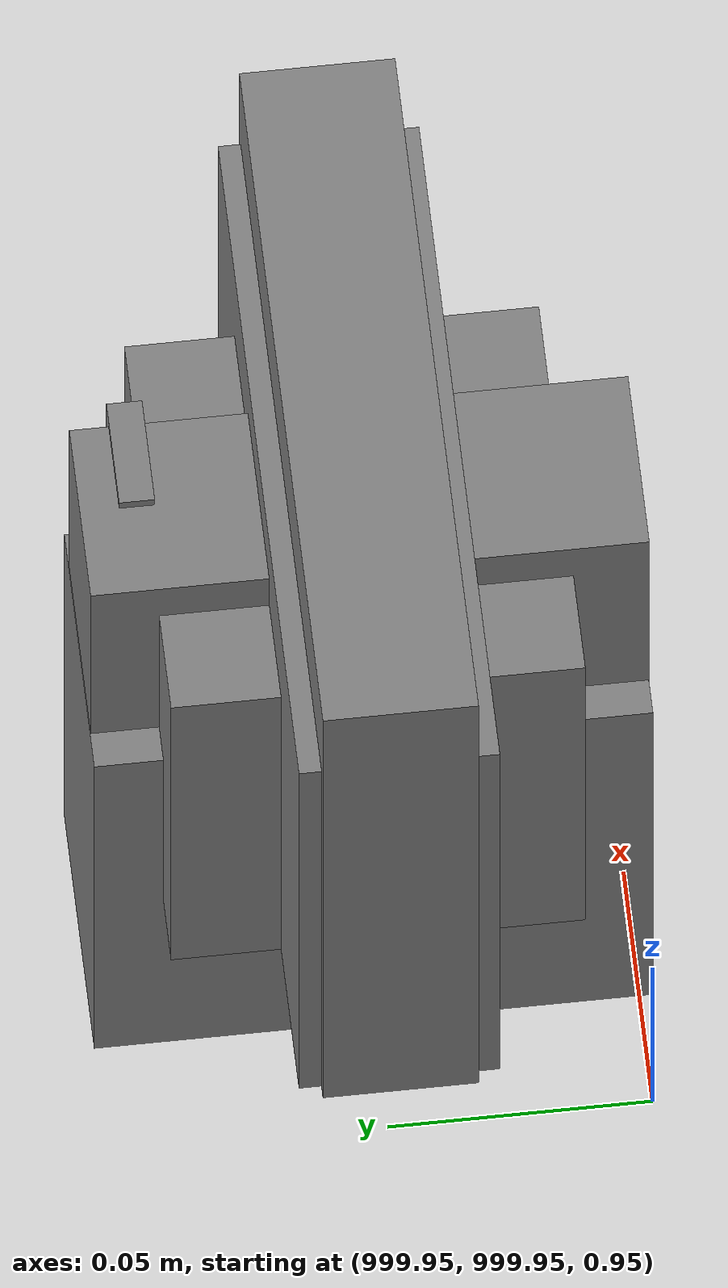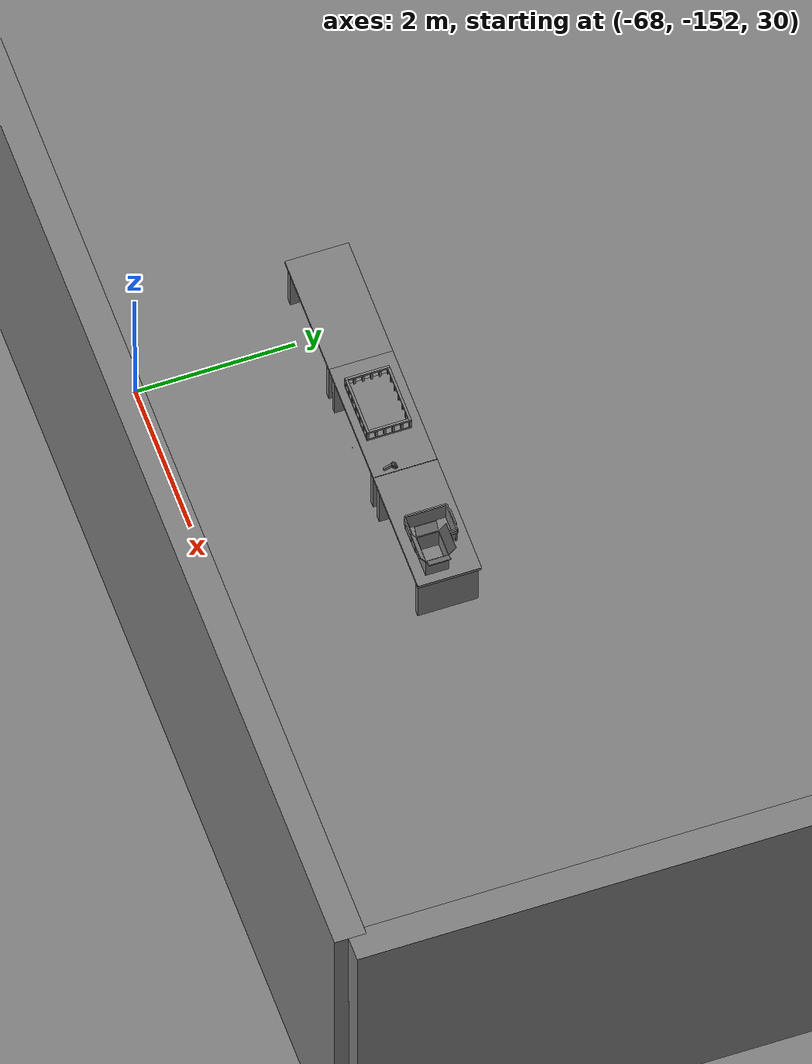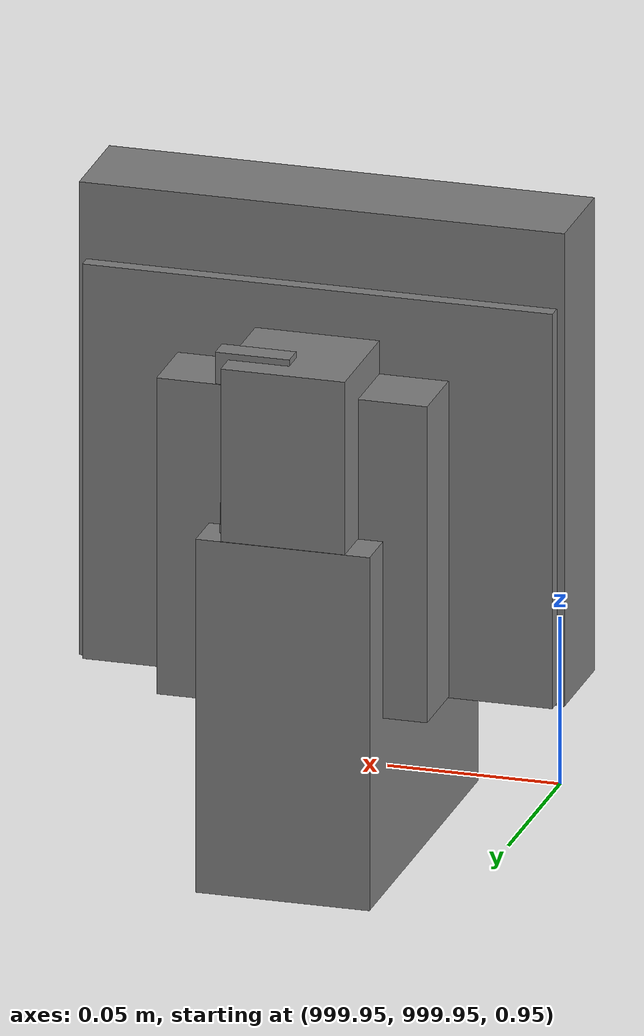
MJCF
<mujoco>
    <option gravity="0.000000000 0.000000000 -9.810000420" timestep="0.0049999999" integrator="implicitfast" density="1.225" viscosity="1.8000001e-05" noslip_iterations="10" iterations="100" sdf_iterations="50">
        <flag multiccd="disable"/>
    </option>
    <size memory="1000M"/>
    <compiler coordinate="local"/>
    <worldbody>
        <light cutoff="30" pos="0 1 1" dir="0 -1 -2"/>
        <light cutoff="30" pos="0 -1 1" dir="0 1 -2"/>
        <body pos="-66.263816833 -149.498565674 31.164999008" euler="141.316940308 61.334918976 -117.794120789" mocap="true" name="spotlight4_SpotLight"/>
        <body pos="1000.000000000 1000.000000000 1.000000000" euler="0.000000000 0.000000000 180.000000000" name="openloong_gripper_2f85_fix_base_usda_battery_01">
            <geom contype="1" conaffinity="1" density="1000" type="box" material="" rgba="0.500000000 0.500000000 0.500000000 1.000000000" solimp="0.899999976 0.949999988 0.001000000" friction="1.000000000 0.005000000 0.000100000" solref="0.020000000 1.000000000" margin="0" condim="3" group="0" pos="-0.011123657 -0.041940309 0.101691343" quat="1.000000000 0.000000000 0.000000000 0.000000000" size="0.010800000 0.003375000 0.004725000" name="openloong_gripper_2f85_fix_base_usda_geom_245974CA_63AC_4130_AF5F_2E0A2D0DB27E"/>
            <geom contype="1" conaffinity="1" density="1000" type="box" material="" rgba="0.500000000 0.500000000 0.500000000 1.000000000" solimp="0.899999976 0.949999988 0.001000000" friction="1.000000000 0.005000000 0.000100000" solref="0.020000000 1.000000000" margin="0" condim="3" group="0" pos="-0.010876465 -0.044247437 0.047066893" quat="0.998702705 -0.050920475 0.000000000 0.000000000" size="0.009450001 0.002700000 0.024975000" name="openloong_gripper_2f85_fix_base_usda_geom_A2E1D26B_F78E_4ECA_AD70_2D608181BECF"/>
            <geom contype="1" conaffinity="1" density="1000" type="box" material="" rgba="0.500000000 0.500000000 0.500000000 1.000000000" solimp="0.899999976 0.949999988 0.001000000" friction="1.000000000 0.005000000 0.000100000" solref="0.020000000 1.000000000" margin="0" condim="3" group="0" pos="-0.001235962 -0.000659180 0.047381196" quat="1.000000000 0.000000000 0.000000000 0.000000000" size="0.039420001 0.039150000 0.047250003" name="openloong_gripper_2f85_fix_base_usda_geom_D4804E3A_B84E_4CB2_8F6C_71DE725309E8"/>
            <geom contype="1" conaffinity="1" density="1000" type="box" material="" rgba="0.500000000 0.500000000 0.500000000 1.000000000" solimp="0.899999976 0.949999988 0.001000000" friction="1.000000000 0.005000000 0.000100000" solref="0.020000000 1.000000000" margin="0" condim="3" group="0" pos="-0.010876465 -0.039138794 0.009851727" quat="1.000000000 0.000000000 0.000000000 0.000000000" size="0.009450001 0.010800000 0.013500000" name="openloong_gripper_2f85_fix_base_usda_geom_D87362FC_DC2B_4D84_AB49_BCDE9CE6BBCA"/>
            <geom contype="1" conaffinity="1" density="1000" type="box" material="" rgba="0.500000000 0.500000000 0.500000000 1.000000000" solimp="0.899999976 0.949999988 0.001000000" friction="1.000000000 0.005000000 0.000100000" solref="0.020000000 1.000000000" margin="0" condim="3" group="0" pos="-0.010876465 -0.041528322 0.071508206" quat="1.000000000 0.000000000 0.000000000 0.000000000" size="0.009450001 0.002700000 0.027000001" name="openloong_gripper_2f85_fix_base_usda_geom_A4CC0D8F_D0D1_4956_82A7_27730CFA4000"/>
            <freejoint name="openloong_gripper_2f85_fix_base_usda_battery_01_joint"/>
            <site size="0.005000000 0.005000000 0.005000000" rgba="0.500000000 0.500000000 0.500000000 1.000000000" pos="0.000000000 0.000000000 0.000000000" quat="0.999961913 0.008726500 0.000000000 0.000000000" group="0" type="sphere" name="openloong_gripper_2f85_fix_base_usda_battery_01site"/>
        </body>
        <body pos="1000.000000000 1000.000000000 1.000000000" euler="0.000000000 0.000000000 180.000000000" name="openloong_gripper_2f85_fix_base_usda_cpu_fan">
            <geom contype="1" conaffinity="1" density="1000" type="box" material="" rgba="0.500000000 0.500000000 0.500000000 1.000000000" solimp="0.899999976 0.949999988 0.001000000" friction="1.000000000 0.005000000 0.000100000" solref="0.020000000 1.000000000" margin="0" condim="3" group="0" pos="0.000000000 0.000000000 0.070034981" quat="0.000000000 0.000000000 0.000000000 1.000000000" size="0.070700005 0.014699999 0.070700005" name="openloong_gripper_2f85_fix_base_usda_geom_CD86BC12_15CE_40C6_90FE_82E39875F8BC"/>
            <freejoint name="openloong_gripper_2f85_fix_base_usda_cpu_fan_joint"/>
            <site size="0.005000000 0.005000000 0.005000000" rgba="0.500000000 0.500000000 0.500000000 1.000000000" pos="0.000000000 0.000000000 0.000000000" quat="0.999961913 0.008726535 0.000000000 0.000000000" group="0" type="sphere" name="openloong_gripper_2f85_fix_base_usda_cpu_fancsite"/>
        </body>
        <body pos="1000.000000000 1000.000000000 1.000000000" euler="0.000000000 0.000000000 180.000000000" name="openloong_gripper_2f85_fix_base_usda_wifi_box">
            <geom contype="1" conaffinity="1" density="1000" type="box" material="" rgba="0.500000000 0.500000000 0.500000000 1.000000000" solimp="0.899999976 0.949999988 0.001000000" friction="1.000000000 0.005000000 0.000100000" solref="0.020000000 1.000000000" margin="0" condim="3" group="0" pos="0.000000000 0.000000000 0.058978677" quat="0.000000000 0.000000047 0.000000000 1.000000000" size="0.068499997 0.018999999 0.059000000" name="openloong_gripper_2f85_fix_base_usda_geom_77C5A706_C611_49B9_8EE6_2E6B99F8840C"/>
            <freejoint name="openloong_gripper_2f85_fix_base_usda_wifi_box_joint"/>
            <site size="0.005000000 0.005000000 0.005000000" rgba="0.500000000 0.500000000 0.500000000 1.000000000" pos="0.000000000 0.000000000 0.000000000" quat="0.999961913 0.008726500 0.000000000 0.000000000" group="0" type="sphere" name="openloong_gripper_2f85_fix_base_usda_wifi_boxsite"/>
        </body>
        <body pos="1000.000000000 1000.000000000 1.000000000" euler="0.000011953 0.000005123 -179.999984741" name="openloong_gripper_2f85_fix_base_usda_intel_box">
            <geom contype="1" conaffinity="1" density="1000" type="box" material="" rgba="0.500000000 0.500000000 0.500000000 1.000000000" solimp="0.899999976 0.949999988 0.001000000" friction="1.000000000 0.005000000 0.000100000" solref="0.020000000 1.000000000" margin="0" condim="3" group="0" pos="0.000000000 -0.000067139 0.000082284" quat="0.707106709 0.000000225 0.000000253 0.707106650" size="0.052800003 0.025300000 0.052800003" name="openloong_gripper_2f85_fix_base_usda_geom_44A135D1_0E47_4C7E_8FE4_432ED6B172FE"/>
            <freejoint name="openloong_gripper_2f85_fix_base_usda_intel_box_joint"/>
            <site size="0.005000000 0.005000000 0.005000000" rgba="0.500000000 0.500000000 0.500000000 1.000000000" pos="0.000000000 0.000000000 0.000000000" quat="0.999961913 0.008726500 0.000000000 0.000000000" group="0" type="sphere" name="openloong_gripper_2f85_fix_base_usda_intel_boxsite"/>
        </body>
        <body pos="1000.000000000 999.999938965 1.000000000" euler="0.000000000 0.000000000 180.000000000" name="openloong_gripper_2f85_fix_base_usda_intelcore_i5">
            <geom contype="1" conaffinity="1" density="1000" type="box" material="" rgba="0.500000000 0.500000000 0.500000000 1.000000000" solimp="0.899999976 0.949999988 0.001000000" friction="1.000000000 0.005000000 0.000100000" solref="0.020000000 1.000000000" margin="0" condim="3" group="0" pos="0.000000000 0.000000000 0.051722717" quat="0.707106709 0.000000000 0.000000000 -0.707106769" size="0.052800000 0.018080002 0.052800000" name="openloong_gripper_2f85_fix_base_usda_geom_AB719C25_B5B7_4F73_9390_9A34C9BDEC0E"/>
            <freejoint name="openloong_gripper_2f85_fix_base_usda_intelcore_i5_joint"/>
            <site size="0.005000000 0.005000000 0.005000000" rgba="0.500000000 0.500000000 0.500000000 1.000000000" pos="0.000000000 0.000000000 0.000000000" quat="0.999961913 0.008726534 0.000000000 0.000000000" group="0" type="sphere" name="openloong_gripper_2f85_fix_base_usda_intelcore_i5site"/>
        </body>
        <body pos="-66.353302002 -149.189147949 31.169118881" euler="45.560821533 -36.549003601 34.344947815" mocap="true" name="spotlight2_SpotLight"/>
        <body pos="-65.939964294 -149.577575684 31.171403885" euler="91.564422607 15.327973366 26.510868073" mocap="true" name="spotlight1_SpotLight"/>
        <body pos="-64.866622925 -149.383972168 30.183746338" euler="89.999984741 89.999946594 0.000000000" name="openloong_gripper_2f85_fix_base_usda_bluebox_01">
            <geom contype="1" conaffinity="1" density="1000" type="box" material="" rgba="0.500000000 0.500000000 0.500000000 1.000000000" solimp="0.899999976 0.949999988 0.001000000" friction="1.000000000 0.005000000 0.000100000" solref="0.020000000 1.000000000" margin="0" condim="3" group="0" pos="0.276580811 0.187225342 0.000068665" quat="0.707106948 0.000077471 0.707106352 0.000077486" size="0.100000001 0.057999998 0.010000000" name="openloong_gripper_2f85_fix_base_usda_geom_9FAAAB91_081E_45F9_ACC4_BE1980699CDF"/>
            <geom contype="1" conaffinity="1" density="1000" type="box" material="" rgba="0.500000000 0.500000000 0.500000000 1.000000000" solimp="0.899999976 0.949999988 0.001000000" friction="1.000000000 0.005000000 0.000100000" solref="0.020000000 1.000000000" margin="0" condim="3" group="0" pos="0.000000000 0.002883911 0.000000000" quat="0.999999881 0.000000000 0.000000000 0.000000000" size="0.254000008 0.003000000 0.172000006" name="openloong_gripper_2f85_fix_base_usda_geom_47C3BD4F_7C5E_4311_86B0_00B125AA020B"/>
            <geom contype="1" conaffinity="1" density="1000" type="box" material="" rgba="0.500000000 0.500000000 0.500000000 1.000000000" solimp="0.899999976 0.949999988 0.001000000" friction="1.000000000 0.005000000 0.000100000" solref="0.020000000 1.000000000" margin="0" condim="3" group="0" pos="0.000000000 0.124874115 0.173484802" quat="0.999796331 0.020176515 -0.000000015 0.000000030" size="0.259999990 0.119999997 0.007000000" name="openloong_gripper_2f85_fix_base_usda_geom_5393B03D_A254_4F80_B2E3_9311F46C0180"/>
            <geom contype="1" conaffinity="1" density="1000" type="box" material="" rgba="0.500000000 0.500000000 0.500000000 1.000000000" solimp="0.899999976 0.949999988 0.001000000" friction="1.000000000 0.005000000 0.000100000" solref="0.020000000 1.000000000" margin="0" condim="3" group="0" pos="0.000000000 0.124874115 -0.173469543" quat="0.999796331 -0.020176545 -0.000000015 0.000000000" size="0.259999990 0.119999997 0.007000000" name="openloong_gripper_2f85_fix_base_usda_geom_C4C54983_7996_4432_AFAE_27609221279C"/>
            <geom contype="1" conaffinity="1" density="1000" type="box" material="" rgba="0.500000000 0.500000000 0.500000000 1.000000000" solimp="0.899999976 0.949999988 0.001000000" friction="1.000000000 0.005000000 0.000100000" solref="0.020000000 1.000000000" margin="0" condim="3" group="0" pos="0.000000000 0.214008331 0.188980103" quat="0.999912977 0.013176724 0.000000015 0.000000000" size="0.259999990 0.029999999 0.012500000" name="openloong_gripper_2f85_fix_base_usda_geom_92AD7DE3_806A_4E03_B58D_EA1D4EAEBC98"/>
            <geom contype="1" conaffinity="1" density="1000" type="box" material="" rgba="0.500000000 0.500000000 0.500000000 1.000000000" solimp="0.899999976 0.949999988 0.001000000" friction="1.000000000 0.005000000 0.000100000" solref="0.020000000 1.000000000" margin="0" condim="3" group="0" pos="-0.258361816 0.125289917 0.001876831" quat="0.702796936 -0.020792112 0.710783124 0.020769298" size="0.189999998 0.119999997 0.009000000" name="openloong_gripper_2f85_fix_base_usda_geom_A498C4C6_EF17_4269_8BFF_3FAFC6554602"/>
            <geom contype="1" conaffinity="1" density="1000" type="box" material="" rgba="0.500000000 0.500000000 0.500000000 1.000000000" solimp="0.899999976 0.949999988 0.001000000" friction="1.000000000 0.005000000 0.000100000" solref="0.020000000 1.000000000" margin="0" condim="3" group="0" pos="0.000000000 0.214008331 -0.188980103" quat="0.999912977 -0.013176769 0.000000030 0.000000015" size="0.259999990 0.029999999 0.012500000" name="openloong_gripper_2f85_fix_base_usda_geom_7994BCBE_EBA1_467D_A2D9_40F75D50B922"/>
            <geom contype="1" conaffinity="1" density="1000" type="box" material="" rgba="0.500000000 0.500000000 0.500000000 1.000000000" solimp="0.899999976 0.949999988 0.001000000" friction="1.000000000 0.005000000 0.000100000" solref="0.020000000 1.000000000" margin="0" condim="3" group="0" pos="-0.276611328 0.187225342 0.000068665" quat="0.707106650 0.000077441 0.707106709 0.000077456" size="0.100000001 0.057999998 0.010000000" name="openloong_gripper_2f85_fix_base_usda_geom_797CBF97_8272_40DA_9D45_E8F9729AFEB1"/>
            <geom contype="1" conaffinity="1" density="1000" type="box" material="" rgba="0.500000000 0.500000000 0.500000000 1.000000000" solimp="0.899999976 0.949999988 0.001000000" friction="1.000000000 0.005000000 0.000100000" solref="0.020000000 1.000000000" margin="0" condim="3" group="0" pos="0.258331299 0.125289917 0.001876831" quat="0.702851415 0.018856421 0.710823774 -0.019329369" size="0.189999998 0.119999997 0.009000000" name="openloong_gripper_2f85_fix_base_usda_geom_CBAC0F45_E019_4D15_9B7E_6B77064DA4B3"/>
            <freejoint name="openloong_gripper_2f85_fix_base_usda_bluebox_01_joint"/>
            <site size="0.005000000 0.005000000 0.005000000" rgba="0.500000000 0.500000000 0.500000000 1.000000000" pos="0.000000000 0.000000000 0.000000000" quat="0.999961913 0.008726534 0.000000000 0.000000000" group="0" type="sphere" name="openloong_gripper_2f85_fix_base_usda_bluebox_01site"/>
        </body>
        <body pos="-64.496299744 -149.491867065 30.235729218" euler="0.000000000 0.000000000 89.999946594" name="openloong_gripper_2f85_fix_base_usda_cardboardbox_01">
            <geom contype="1" conaffinity="1" density="1000" type="box" material="" rgba="0.500000000 0.500000000 0.500000000 1.000000000" solimp="0.899999976 0.949999988 0.001000000" friction="1.000000000 0.005000000 0.000100000" solref="0.020000000 1.000000000" margin="0" condim="3" group="0" pos="-0.003166199 -0.004086494 0.005052090" quat="1.000000000 0.000000000 0.000000000 0.000000000" size="0.142499998 0.177500010 0.005000000" name="openloong_gripper_2f85_fix_base_usda_geom_20ADE133_349B_493C_BF42_65B462B8C0BD"/>
            <geom contype="1" conaffinity="1" density="1000" type="box" material="" rgba="0.500000000 0.500000000 0.500000000 1.000000000" solimp="0.899999976 0.949999988 0.001000000" friction="1.000000000 0.005000000 0.000100000" solref="0.020000000 1.000000000" margin="0" condim="3" group="0" pos="-0.003166199 0.170316696 0.150570869" quat="1.000000000 0.000000000 0.000000000 0.000000000" size="0.142499998 0.005000000 0.149999991" name="openloong_gripper_2f85_fix_base_usda_geom_DAC37BE3_3367_4457_AD4A_7D5B3DE2DF05"/>
            <geom contype="1" conaffinity="1" density="1000" type="box" material="" rgba="0.500000000 0.500000000 0.500000000 1.000000000" solimp="0.899999976 0.949999988 0.001000000" friction="1.000000000 0.005000000 0.000100000" solref="0.020000000 1.000000000" margin="0" condim="3" group="0" pos="-0.147399902 -0.005307198 0.150570869" quat="1.000000000 0.000000000 0.000000000 0.000000000" size="0.005000000 0.177500010 0.149999991" name="openloong_gripper_2f85_fix_base_usda_geom_B99518A7_65B2_4762_BC98_CD1BA61744B0"/>
            <geom contype="1" conaffinity="1" density="1000" type="box" material="" rgba="0.500000000 0.500000000 0.500000000 1.000000000" solimp="0.899999976 0.949999988 0.001000000" friction="1.000000000 0.005000000 0.000100000" solref="0.020000000 1.000000000" margin="0" condim="3" group="0" pos="0.140275955 -0.005307198 0.150570869" quat="1.000000000 0.000000000 0.000000000 0.000000000" size="0.005000000 0.177500010 0.149999991" name="openloong_gripper_2f85_fix_base_usda_geom_FF608699_77D6_4D68_97B5_3FA4B81A5758"/>
            <geom contype="1" conaffinity="1" density="1000" type="box" material="" rgba="0.500000000 0.500000000 0.500000000 1.000000000" solimp="0.899999976 0.949999988 0.001000000" friction="1.000000000 0.005000000 0.000100000" solref="0.020000000 1.000000000" margin="0" condim="3" group="0" pos="-0.003166199 -0.181550980 0.150570869" quat="1.000000000 0.000000000 0.000000000 0.000000000" size="0.142499998 0.005000000 0.149999991" name="openloong_gripper_2f85_fix_base_usda_geom_37AEB677_7C93_47F9_9756_CAE9B63D8F5A"/>
            <freejoint name="openloong_gripper_2f85_fix_base_usda_cardboardbox_01_joint"/>
            <site size="0.005000000 0.005000000 0.005000000" rgba="0.500000000 0.500000000 0.500000000 1.000000000" pos="0.000000000 0.000000000 0.000000000" quat="0.999961913 0.008726535 0.000000000 0.000000000" group="0" type="sphere" name="openloong_gripper_2f85_fix_base_usda_site_16A18DFE_D035_47A4_8BF1_223F476FF552"/>
            <body pos="0.139160156 -0.004048347 0.301930904" euler="-179.999954224 49.383502960 179.999954224" name="openloong_gripper_2f85_fix_base_usda_A1_006">
                <geom contype="1" conaffinity="1" density="1000" type="box" material="" rgba="0.500000000 0.500000000 0.500000000 1.000000000" solimp="0.899999976 0.949999988 0.001000000" friction="1.000000000 0.005000000 0.000100000" solref="0.020000000 1.000000000" margin="0" condim="3" group="0" pos="-0.071587563 0.000009537 0.001745224" quat="0.999999881 0.000000000 0.000000000 0.000000000" size="0.071249999 0.179999992 0.002500000" name="openloong_gripper_2f85_fix_base_usda_geom_0AD5C330_51D2_4099_8421_EA2867B5CFFE"/>
                <joint armature="0" stiffness="0.07" damping="0.0099999998" axis="0.000000 1.000000 0.000000" type="hinge" name="openloong_gripper_2f85_fix_base_usda_A1_006"/>
            </body>
            <body pos="-0.145902634 -0.004086494 0.301938057" euler="-180.000000000 -60.000011444 -180.000000000" name="openloong_gripper_2f85_fix_base_usda_A2_006">
                <geom contype="1" conaffinity="1" density="1000" type="box" material="" rgba="0.500000000 0.500000000 0.500000000 1.000000000" solimp="0.899999976 0.949999988 0.001000000" friction="1.000000000 0.005000000 0.000100000" solref="0.020000000 1.000000000" margin="0" condim="3" group="0" pos="0.071268082 0.000009537 0.002717972" quat="0.000002921 0.000000000 -0.000000030 0.999999881" size="0.071249999 0.179999992 0.002500000" name="openloong_gripper_2f85_fix_base_usda_geom_1EE4D19F_A3AF_48FE_A70D_F0DAF32F0EED"/>
                <joint armature="0" stiffness="0.07" damping="0.0099999998" axis="0.000000 1.000000 0.000000" type="hinge" name="openloong_gripper_2f85_fix_base_usda_A2_006"/>
            </body>
            <body pos="-0.003385544 0.175991058 0.301930904" euler="-125.858116150 -0.000004561 0.000002331" name="openloong_gripper_2f85_fix_base_usda_B2_006">
                <geom contype="1" conaffinity="1" density="1000" type="box" material="" rgba="0.500000000 0.500000000 0.500000000 1.000000000" solimp="0.899999976 0.949999988 0.001000000" friction="1.000000000 0.005000000 0.000100000" solref="0.020000000 1.000000000" margin="0" condim="3" group="0" pos="0.000009537 -0.070939064 -0.002470016" quat="0.999614120 0.027776197 -0.000000015 0.000000030" size="0.137500003 0.064999998 0.005000000" name="openloong_gripper_2f85_fix_base_usda_geom_43F85954_CDBE_47AE_A41A_B3C8DB845042"/>
                <joint armature="0" stiffness="0.07" damping="0.0099999998" axis="1.000000 0.000000 0.000000" type="hinge" name="openloong_gripper_2f85_fix_base_usda_B2_006"/>
            </body>
            <body pos="-0.003385544 -0.184140205 0.301938057" euler="147.805557251 0.000000000 0.000000000" name="openloong_gripper_2f85_fix_base_usda_B1_006">
                <geom contype="1" conaffinity="1" density="1000" type="box" material="" rgba="0.500000000 0.500000000 0.500000000 1.000000000" solimp="0.899999976 0.949999988 0.001000000" friction="1.000000000 0.005000000 0.000100000" solref="0.020000000 1.000000000" margin="0" condim="3" group="0" pos="-0.000028610 0.070202351 -0.002703667" quat="0.999614179 -0.027776167 0.000000000 0.000000000" size="0.137500003 0.064999998 0.005000000" name="openloong_gripper_2f85_fix_base_usda_geom_0213E6EC_DCBE_4D46_94A2_59B4D98E35F9"/>
                <joint armature="0" stiffness="0.07" damping="0.0099999998" axis="1.000000 0.000000 0.000000" type="hinge" name="openloong_gripper_2f85_fix_base_usda_B1_006"/>
            </body>
        </body>
        <body pos="-65.882858276 -149.481979370 30.229999542" euler="-64.487716675 0.000000000 0.000000000" name="openloong_gripper_2f85_fix_base_usda_Barcode">
            <geom contype="1" conaffinity="1" density="1000" type="box" material="" rgba="0.500000000 0.500000000 0.500000000 1.000000000" solimp="0.899999976 0.949999988 0.001000000" friction="1.000000000 0.005000000 0.000100000" solref="0.020000000 1.000000000" margin="0" condim="3" group="0" pos="0.000000000 0.013038635 0.001419067" quat="0.000000000 0.000000000 0.000000000 1.000000119" size="0.034000002 0.010000000 0.017999999" name="openloong_gripper_2f85_fix_base_usda_geom_F497950C_B3AB_452C_A431_640B0F7F9AD0"/>
            <geom contype="1" conaffinity="1" density="1000" type="box" material="" rgba="0.500000000 0.500000000 0.500000000 1.000000000" solimp="0.899999976 0.949999988 0.001000000" friction="1.000000000 0.005000000 0.000100000" solref="0.020000000 1.000000000" margin="0" condim="3" group="0" pos="0.000000000 -0.035301208 -0.007095337" quat="0.000000000 0.000000000 -0.043619365 0.999048233" size="0.028999999 0.010000000 0.020000000" name="openloong_gripper_2f85_fix_base_usda_geom_0CC0A79C_19DA_4A29_A14B_AFFBE919AFF1"/>
            <geom contype="1" conaffinity="1" density="1000" type="box" material="" rgba="0.500000000 0.500000000 0.500000000 1.000000000" solimp="0.899999976 0.949999988 0.001000000" friction="1.000000000 0.005000000 0.000100000" solref="0.020000000 1.000000000" margin="0" condim="3" group="0" pos="0.000000000 -0.043411255 -0.011749268" quat="0.922262907 0.386563420 0.000000000 0.000000000" size="0.026000001 0.010000000 0.020000000" name="openloong_gripper_2f85_fix_base_usda_geom_B807599A_F719_4764_8BA2_892A3800BC2A"/>
            <geom contype="1" conaffinity="1" density="1000" type="box" material="" rgba="0.500000000 0.500000000 0.500000000 1.000000000" solimp="0.899999976 0.949999988 0.001000000" friction="1.000000000 0.005000000 0.000100000" solref="0.020000000 1.000000000" margin="0" condim="3" group="0" pos="0.000000000 -0.016967773 -0.031860352" quat="0.000000000 0.000000000 0.000000000 1.000000119" size="0.008000000 0.010000000 0.013000000" name="openloong_gripper_2f85_fix_base_usda_geom_AF8BE279_ED1E_448B_BEAC_6FAAE016D3A4"/>
            <geom contype="1" conaffinity="1" density="1000" type="box" material="" rgba="0.500000000 0.500000000 0.500000000 1.000000000" solimp="0.899999976 0.949999988 0.001000000" friction="1.000000000 0.005000000 0.000100000" solref="0.020000000 1.000000000" margin="0" condim="3" group="0" pos="0.000000000 -0.001869202 0.000312805" quat="0.953716993 0.300705761 0.000000000 0.000000000" size="0.032000002 0.010000000 0.018999999" name="openloong_gripper_2f85_fix_base_usda_geom_B26867FC_4B47_49E6_A71A_A6D93BE50451"/>
            <geom contype="1" conaffinity="1" density="1000" type="box" material="" rgba="0.500000000 0.500000000 0.500000000 1.000000000" solimp="0.899999976 0.949999988 0.001000000" friction="1.000000000 0.005000000 0.000100000" solref="0.020000000 1.000000000" margin="0" condim="3" group="0" pos="0.000000000 -0.019531250 -0.003173828" quat="0.953716993 0.300705761 0.000000000 0.000000000" size="0.030999999 0.010000000 0.020000000" name="openloong_gripper_2f85_fix_base_usda_geom_FD95E8AD_BF21_4D19_9DF7_E17B2AC984E8"/>
            <geom contype="1" conaffinity="1" density="1000" type="box" material="" rgba="0.500000000 0.500000000 0.500000000 1.000000000" solimp="0.899999976 0.949999988 0.001000000" friction="1.000000000 0.005000000 0.000100000" solref="0.020000000 1.000000000" margin="0" condim="3" group="0" pos="0.000000000 -0.035301208 -0.007095337" quat="0.953716993 0.300705761 0.000000000 0.000000000" size="0.028999999 0.010000000 0.020000000" name="openloong_gripper_2f85_fix_base_usda_geom_6D4ADE1F_822A_434F_A246_F89CE7519B9E"/>
            <geom contype="1" conaffinity="1" density="1000" type="box" material="" rgba="0.500000000 0.500000000 0.500000000 1.000000000" solimp="0.899999976 0.949999988 0.001000000" friction="1.000000000 0.005000000 0.000100000" solref="0.020000000 1.000000000" margin="0" condim="3" group="0" pos="0.000000000 -0.042617798 -0.071121216" quat="0.000000000 0.000000000 0.000000000 1.000000119" size="0.013000000 0.021000000 0.059999999" name="openloong_gripper_2f85_fix_base_usda_geom_22D4AAB2_D0C0_4E46_9247_6D0E4760194E"/>
            <freejoint name="openloong_gripper_2f85_fix_base_usda_Barcode_joint"/>
            <site size="0.005000000 0.005000000 0.005000000" rgba="0.500000000 0.500000000 0.500000000 1.000000000" pos="0.000000000 0.000000000 0.000000000" quat="1.000000000 0.000000000 0.000000000 0.000000000" group="0" type="sphere" name="openloong_gripper_2f85_fix_base_usda_Barcode_site"/>
        </body>
        <body pos="-66.745018005 -149.392349243 30.184000015" euler="0.000000000 0.000000000 89.999946594" name="[22330291364134]_Basket_01">
            <geom contype="1" conaffinity="1" density="1000" type="box" material="" rgba="0.500000000 0.500000000 0.500000000 1.000000000" solimp="0.899999976 0.949999988 0.001000000" friction="1.000000000 0.005000000 0.000100000" solref="0.020000000 1.000000000" margin="0" condim="3" group="0" pos="-0.052425385 0.389207840 0.089787483" quat="0.707107008 0.000000000 0.000000000 0.707106411" size="0.014249999 0.014249999 0.059999999" name="[22330291364134]_geom_E5AB7117_1B56_4E92_B999_58B3880465E8"/>
            <geom contype="1" conaffinity="1" density="1000" type="box" material="" rgba="0.500000000 0.500000000 0.500000000 1.000000000" solimp="0.899999976 0.949999988 0.001000000" friction="1.000000000 0.005000000 0.000100000" solref="0.020000000 1.000000000" margin="0" condim="3" group="0" pos="0.264015198 -0.133043289 0.089787483" quat="0.707107008 0.000000000 0.000000000 0.707106411" size="0.014249999 0.014249999 0.059999999" name="[22330291364134]_geom_0F178C9E_44F7_4D97_AA99_1162BDB101EA"/>
            <geom contype="1" conaffinity="1" density="1000" type="box" material="" rgba="0.500000000 0.500000000 0.500000000 1.000000000" solimp="0.899999976 0.949999988 0.001000000" friction="1.000000000 0.005000000 0.000100000" solref="0.020000000 1.000000000" margin="0" condim="3" group="0" pos="-0.264015198 -0.265548706 0.089793205" quat="0.707107008 0.000000000 0.000000000 0.707106411" size="0.014249999 0.014249999 0.059999999" name="[22330291364134]_geom_9E3A3CD5_26D5_40CB_9C41_B2767CE08582"/>
            <geom contype="1" conaffinity="1" density="1000" type="box" material="" rgba="0.500000000 0.500000000 0.500000000 1.000000000" solimp="0.899999976 0.949999988 0.001000000" friction="1.000000000 0.005000000 0.000100000" solref="0.020000000 1.000000000" margin="0" condim="3" group="0" pos="-0.160263062 -0.389322281 0.089793205" quat="0.707107008 0.000000000 0.000000000 0.707106411" size="0.014249999 0.014249999 0.059999999" name="[22330291364134]_geom_21B9C8D3_F895_4032_B3D2_5CFB77976D53"/>
            <geom contype="1" conaffinity="1" density="1000" type="box" material="" rgba="0.500000000 0.500000000 0.500000000 1.000000000" solimp="0.899999976 0.949999988 0.001000000" friction="1.000000000 0.005000000 0.000100000" solref="0.020000000 1.000000000" margin="0" condim="3" group="0" pos="0.162265778 -0.389322281 0.089787483" quat="0.707107008 0.000000000 0.000000000 0.707106411" size="0.014249999 0.014249999 0.059999999" name="[22330291364134]_geom_5C7B3AEB_E2A7_4D13_9D62_21ED949C7899"/>
            <geom contype="1" conaffinity="1" density="1000" type="box" material="" rgba="0.500000000 0.500000000 0.500000000 1.000000000" solimp="0.899999976 0.949999988 0.001000000" friction="1.000000000 0.005000000 0.000100000" solref="0.020000000 1.000000000" margin="0" condim="3" group="0" pos="0.264015198 0.389207840 0.089787483" quat="0.707107008 0.000000000 0.000000000 0.707106411" size="0.014249999 0.014249999 0.059999999" name="[22330291364134]_geom_78C3D6AA_B163_48F5_9196_1DD48824BEE7"/>
            <geom contype="1" conaffinity="1" density="1000" type="box" material="" rgba="0.500000000 0.500000000 0.500000000 1.000000000" solimp="0.899999976 0.949999988 0.001000000" friction="1.000000000 0.005000000 0.000100000" solref="0.020000000 1.000000000" margin="0" condim="3" group="0" pos="-0.264015198 -0.133043289 0.089793205" quat="0.707107008 0.000000000 0.000000000 0.707106411" size="0.014249999 0.014249999 0.059999999" name="[22330291364134]_geom_AC4BF79B_3639_4403_99E6_492C740E7D55"/>
            <geom contype="1" conaffinity="1" density="1000" type="box" material="" rgba="0.500000000 0.500000000 0.500000000 1.000000000" solimp="0.899999976 0.949999988 0.001000000" friction="1.000000000 0.005000000 0.000100000" solref="0.020000000 1.000000000" margin="0" condim="3" group="0" pos="-0.264026642 0.269256592 0.089793205" quat="0.707107008 0.000000000 0.000000000 0.707106411" size="0.014249999 0.014249999 0.059999999" name="[22330291364134]_geom_581338AC_D4B8_4302_B212_6B8484F5F720"/>
            <geom contype="1" conaffinity="1" density="1000" type="box" material="" rgba="0.500000000 0.500000000 0.500000000 1.000000000" solimp="0.899999976 0.949999988 0.001000000" friction="1.000000000 0.005000000 0.000100000" solref="0.020000000 1.000000000" margin="0" condim="3" group="0" pos="0.054462433 0.389207840 0.089787483" quat="0.707107008 0.000000000 0.000000000 0.707106411" size="0.014249999 0.014249999 0.059999999" name="[22330291364134]_geom_0830EF4F_5237_43C8_B229_C7073C427BC2"/>
            <geom contype="1" conaffinity="1" density="1000" type="box" material="" rgba="0.500000000 0.500000000 0.500000000 1.000000000" solimp="0.899999976 0.949999988 0.001000000" friction="1.000000000 0.005000000 0.000100000" solref="0.020000000 1.000000000" margin="0" condim="3" group="0" pos="0.054462433 -0.389322281 0.089787483" quat="0.707107008 0.000000000 0.000000000 0.707106411" size="0.014249999 0.014249999 0.059999999" name="[22330291364134]_geom_9DD5C63B_54D2_4DBE_8A60_67309D8C52CD"/>
            <geom contype="1" conaffinity="1" density="1000" type="box" material="" rgba="0.500000000 0.500000000 0.500000000 1.000000000" solimp="0.899999976 0.949999988 0.001000000" friction="1.000000000 0.005000000 0.000100000" solref="0.020000000 1.000000000" margin="0" condim="3" group="0" pos="0.264015198 0.269256592 0.089793205" quat="0.707107008 0.000000000 0.000000000 0.707106411" size="0.014249999 0.014249999 0.059999999" name="[22330291364134]_geom_D95519F7_76E6_406A_A36F_B58F482ABF32"/>
            <geom contype="1" conaffinity="1" density="1000" type="box" material="" rgba="0.500000000 0.500000000 0.500000000 1.000000000" solimp="0.899999976 0.949999988 0.001000000" friction="1.000000000 0.005000000 0.000100000" solref="0.020000000 1.000000000" margin="0" condim="3" group="0" pos="0.264015198 -0.389322281 0.089787483" quat="0.707107008 0.000000000 0.000000000 0.707106411" size="0.014249999 0.014249999 0.059999999" name="[22330291364134]_geom_979FD894_450A_4CE2_B2FB_F64D30E5C697"/>
            <geom contype="1" conaffinity="1" density="1000" type="box" material="" rgba="0.500000000 0.500000000 0.500000000 1.000000000" solimp="0.899999976 0.949999988 0.001000000" friction="1.000000000 0.005000000 0.000100000" solref="0.020000000 1.000000000" margin="0" condim="3" group="0" pos="0.000000000 0.000000000 0.015998840" quat="0.707107008 0.000000000 0.000000000 0.707106411" size="0.403499991 0.279000014 0.015750000" name="[22330291364134]_geom_989AD0C8_69B6_4A2B_8551_8F7294D37F15"/>
            <geom contype="1" conaffinity="1" density="1000" type="box" material="" rgba="0.500000000 0.500000000 0.500000000 1.000000000" solimp="0.899999976 0.949999988 0.001000000" friction="1.000000000 0.005000000 0.000100000" solref="0.020000000 1.000000000" margin="0" condim="3" group="0" pos="0.000000000 -0.389476776 0.163619041" quat="0.707107008 0.000000000 0.000000000 0.707106411" size="0.015000000 0.277500004 0.015750000" name="[22330291364134]_geom_63CEAF0D_434C_4AFC_A62D_E8C523F361D9"/>
            <geom contype="1" conaffinity="1" density="1000" type="box" material="" rgba="0.500000000 0.500000000 0.500000000 1.000000000" solimp="0.899999976 0.949999988 0.001000000" friction="1.000000000 0.005000000 0.000100000" solref="0.020000000 1.000000000" margin="0" condim="3" group="0" pos="0.162265778 0.389207840 0.089787483" quat="0.707107008 0.000000000 0.000000000 0.707106411" size="0.014249999 0.014249999 0.059999999" name="[22330291364134]_geom_8C715C3A_D30D_45AD_8B5A_2581D055D189"/>
            <geom contype="1" conaffinity="1" density="1000" type="box" material="" rgba="0.500000000 0.500000000 0.500000000 1.000000000" solimp="0.899999976 0.949999988 0.001000000" friction="1.000000000 0.005000000 0.000100000" solref="0.020000000 1.000000000" margin="0" condim="3" group="0" pos="0.000000000 0.389471054 0.163619041" quat="0.707107008 0.000000000 0.000000000 0.707106411" size="0.015000000 0.277500004 0.015750000" name="[22330291364134]_geom_87B5C34C_B56D_4244_BA61_FF7C6218CD64"/>
            <geom contype="1" conaffinity="1" density="1000" type="box" material="" rgba="0.500000000 0.500000000 0.500000000 1.000000000" solimp="0.899999976 0.949999988 0.001000000" friction="1.000000000 0.005000000 0.000100000" solref="0.020000000 1.000000000" margin="0" condim="3" group="0" pos="-0.263511658 0.000000000 0.163619041" quat="0.707107008 0.000000000 0.000000000 0.707106411" size="0.403499991 0.015000000 0.015750000" name="[22330291364134]_geom_479EF20F_D58E_495D_9B3F_F9F3C1078C02"/>
            <geom contype="1" conaffinity="1" density="1000" type="box" material="" rgba="0.500000000 0.500000000 0.500000000 1.000000000" solimp="0.899999976 0.949999988 0.001000000" friction="1.000000000 0.005000000 0.000100000" solref="0.020000000 1.000000000" margin="0" condim="3" group="0" pos="-0.264015198 0.141334534 0.089793205" quat="0.707107008 0.000000000 0.000000000 0.707106411" size="0.014249999 0.014249999 0.059999999" name="[22330291364134]_geom_1A733A74_2CED_49D5_84D0_6EE55CD82D51"/>
            <geom contype="1" conaffinity="1" density="1000" type="box" material="" rgba="0.500000000 0.500000000 0.500000000 1.000000000" solimp="0.899999976 0.949999988 0.001000000" friction="1.000000000 0.005000000 0.000100000" solref="0.020000000 1.000000000" margin="0" condim="3" group="0" pos="0.264015198 -0.265548706 0.089787483" quat="0.707107008 0.000000000 0.000000000 0.707106411" size="0.014249999 0.014249999 0.059999999" name="[22330291364134]_geom_5DD62349_DEF1_4B88_990C_4F8FD7F66B94"/>
            <geom contype="1" conaffinity="1" density="1000" type="box" material="" rgba="0.500000000 0.500000000 0.500000000 1.000000000" solimp="0.899999976 0.949999988 0.001000000" friction="1.000000000 0.005000000 0.000100000" solref="0.020000000 1.000000000" margin="0" condim="3" group="0" pos="-0.160263062 0.389207840 0.089787483" quat="0.707107008 0.000000000 0.000000000 0.707106411" size="0.014249999 0.014249999 0.059999999" name="[22330291364134]_geom_14EA1049_98BA_46BA_8F1F_27E0899A1903"/>
            <geom contype="1" conaffinity="1" density="1000" type="box" material="" rgba="0.500000000 0.500000000 0.500000000 1.000000000" solimp="0.899999976 0.949999988 0.001000000" friction="1.000000000 0.005000000 0.000100000" solref="0.020000000 1.000000000" margin="0" condim="3" group="0" pos="-0.052425385 -0.389322281 0.089787483" quat="0.707107008 0.000000000 0.000000000 0.707106411" size="0.014249999 0.014249999 0.059999999" name="[22330291364134]_geom_462B485C_5554_4C10_8656_5F25E9B20B7A"/>
            <geom contype="1" conaffinity="1" density="1000" type="box" material="" rgba="0.500000000 0.500000000 0.500000000 1.000000000" solimp="0.899999976 0.949999988 0.001000000" friction="1.000000000 0.005000000 0.000100000" solref="0.020000000 1.000000000" margin="0" condim="3" group="0" pos="-0.264026642 -0.389322281 0.089793205" quat="0.707107008 0.000000000 0.000000000 0.707106411" size="0.014249999 0.014249999 0.059999999" name="[22330291364134]_geom_0F490FA3_CCB4_4D07_8CEA_21CFC82042F3"/>
            <geom contype="1" conaffinity="1" density="1000" type="box" material="" rgba="0.500000000 0.500000000 0.500000000 1.000000000" solimp="0.899999976 0.949999988 0.001000000" friction="1.000000000 0.005000000 0.000100000" solref="0.020000000 1.000000000" margin="0" condim="3" group="0" pos="0.264015198 0.141334534 0.089787483" quat="0.707107008 0.000000000 0.000000000 0.707106411" size="0.014249999 0.014249999 0.059999999" name="[22330291364134]_geom_42BC79EA_AB7A_45DD_ADC6_D74E9DB9DF8C"/>
            <geom contype="1" conaffinity="1" density="1000" type="box" material="" rgba="0.500000000 0.500000000 0.500000000 1.000000000" solimp="0.899999976 0.949999988 0.001000000" friction="1.000000000 0.005000000 0.000100000" solref="0.020000000 1.000000000" margin="0" condim="3" group="0" pos="-0.264015198 0.389207840 0.089793205" quat="0.707107008 0.000000000 0.000000000 0.707106411" size="0.014249999 0.014249999 0.059999999" name="[22330291364134]_geom_3260A44C_096A_4B79_BEFF_E0772C7609EF"/>
            <geom contype="1" conaffinity="1" density="1000" type="box" material="" rgba="0.500000000 0.500000000 0.500000000 1.000000000" solimp="0.899999976 0.949999988 0.001000000" friction="1.000000000 0.005000000 0.000100000" solref="0.020000000 1.000000000" margin="0" condim="3" group="0" pos="0.264015198 0.004480362 0.089787483" quat="0.707107008 0.000000000 0.000000000 0.707106411" size="0.014249999 0.014249999 0.059999999" name="[22330291364134]_geom_7BAE71FF_561B_4011_8B07_0AD371773605"/>
            <geom contype="1" conaffinity="1" density="1000" type="box" material="" rgba="0.500000000 0.500000000 0.500000000 1.000000000" solimp="0.899999976 0.949999988 0.001000000" friction="1.000000000 0.005000000 0.000100000" solref="0.020000000 1.000000000" margin="0" condim="3" group="0" pos="0.263694763 -0.000011444 0.163619041" quat="0.707107008 0.000000000 0.000000000 0.707106411" size="0.403499991 0.015000000 0.015750000" name="[22330291364134]_geom_489E5814_2818_4E87_A227_E2C698505BF3"/>
            <geom contype="1" conaffinity="1" density="1000" type="box" material="" rgba="0.500000000 0.500000000 0.500000000 1.000000000" solimp="0.899999976 0.949999988 0.001000000" friction="1.000000000 0.005000000 0.000100000" solref="0.020000000 1.000000000" margin="0" condim="3" group="0" pos="-0.264015198 0.004480362 0.089793205" quat="0.707107008 0.000000000 0.000000000 0.707106411" size="0.014249999 0.014249999 0.059999999" name="[22330291364134]_geom_21AB61EB_DED1_43A1_8295_BE9320E81330"/>
            <freejoint name="[22330291364134]_joint_31CB7FF1_8DC6_44C3_A983_D5057536BE0C"/>
        </body>
        <body pos="0.000000000 0.000000000 0.000000000" euler="0.000000000 0.000000000 0.000000000" name="Static Objects_Static Objects">
            <geom contype="1" conaffinity="1" density="1000" type="box" material="" rgba="0.500000000 0.500000000 0.500000000 1.000000000" solimp="0.899999976 0.949999988 0.001000000" friction="1.000000000 0.005000000 0.000100000" solref="0.020000000 1.000000000" margin="0" condim="3" group="0" pos="-67.544113159 -149.365814209 29.727830887" quat="0.500000417 0.499999970 0.499999553 0.499999970" size="0.381000012 0.319999993 0.041000001" name="Static Objects_geom_1446D720_ED30_4256_8628_FEFB502CC8E9"/>
            <geom contype="1" conaffinity="1" density="1000" type="box" material="" rgba="0.500000000 0.500000000 0.500000000 1.000000000" solimp="0.899999976 0.949999988 0.001000000" friction="1.000000000 0.005000000 0.000100000" solref="0.020000000 1.000000000" margin="0" condim="3" group="0" pos="-68.239501953 -149.365814209 30.086868286" quat="0.500000417 0.499999970 0.499999553 0.499999970" size="0.370999992 0.039500002 0.745000005" name="Static Objects_geom_5CA7D07B_68C9_4D3D_8C7E_ED1ACC0E402E"/>
            <geom contype="1" conaffinity="1" density="1000" type="box" material="" rgba="0.500000000 0.500000000 0.500000000 1.000000000" solimp="0.899999976 0.949999988 0.001000000" friction="1.000000000 0.005000000 0.000100000" solref="0.020000000 1.000000000" margin="0" condim="3" group="0" pos="-68.239501953 -149.365814209 30.147235870" quat="0.500000417 0.499999970 0.499999553 0.499999970" size="0.400000006 0.022000000 0.800000012" name="Static Objects_geom_09F6FDD2_81BC_4ADC_87EA_6A342B25C477"/>
            <geom contype="1" conaffinity="1" density="1000" type="box" material="" rgba="0.500000000 0.500000000 0.500000000 1.000000000" solimp="0.899999976 0.949999988 0.001000000" friction="1.000000000 0.005000000 0.000100000" solref="0.020000000 1.000000000" margin="0" condim="3" group="0" pos="-68.934890747 -149.365814209 29.727830887" quat="0.500000417 0.499999970 0.499999553 0.499999970" size="0.381000012 0.319999993 0.041000001" name="Static Objects_geom_5FF1033A_197E_4023_B199_020FC14A0E31"/>
            <geom contype="1" conaffinity="1" density="1000" type="box" material="" rgba="0.500000000 0.500000000 0.500000000 1.000000000" solimp="0.899999976 0.949999988 0.001000000" friction="1.000000000 0.005000000 0.000100000" solref="0.020000000 1.000000000" margin="0" condim="3" group="0" pos="-68.239501953 -149.365814209 29.561563492" quat="0.500000417 0.499999970 0.499999553 0.499999970" size="0.020000000 0.022000000 0.660000026" name="Static Objects_geom_8D95DDF0_AD3F_49E9_B377_52CA133E75C0"/>
            <geom contype="1" conaffinity="1" density="1000" type="box" material="" rgba="0.500000000 0.500000000 0.500000000 1.000000000" solimp="0.899999976 0.949999988 0.001000000" friction="1.000000000 0.005000000 0.000100000" solref="0.020000000 1.000000000" margin="0" condim="3" group="0" pos="-65.945671082 -149.365814209 29.727830887" quat="0.500000417 0.499999970 0.499999553 0.499999970" size="0.381000012 0.319999993 0.041000001" name="Static Objects_geom_7EDE127F_60AA_495D_A0A7_66CE0B6DDB22"/>
            <geom contype="1" conaffinity="1" density="1000" type="box" material="" rgba="0.500000000 0.500000000 0.500000000 1.000000000" solimp="0.899999976 0.949999988 0.001000000" friction="1.000000000 0.005000000 0.000100000" solref="0.020000000 1.000000000" margin="0" condim="3" group="0" pos="-66.641059875 -149.365814209 30.086868286" quat="0.500000417 0.499999970 0.499999553 0.499999970" size="0.370999992 0.039500002 0.745000005" name="Static Objects_geom_40A07B40_6B7D_4E87_9B10_D16753F91B57"/>
            <geom contype="1" conaffinity="1" density="1000" type="box" material="" rgba="0.500000000 0.500000000 0.500000000 1.000000000" solimp="0.899999976 0.949999988 0.001000000" friction="1.000000000 0.005000000 0.000100000" solref="0.020000000 1.000000000" margin="0" condim="3" group="0" pos="-66.641059875 -149.365814209 30.147235870" quat="0.500000417 0.499999970 0.499999553 0.499999970" size="0.400000006 0.022000000 0.800000012" name="Static Objects_geom_E564C297_2686_4EF8_A249_8DFAFDDE174C"/>
            <geom contype="1" conaffinity="1" density="1000" type="box" material="" rgba="0.500000000 0.500000000 0.500000000 1.000000000" solimp="0.899999976 0.949999988 0.001000000" friction="1.000000000 0.005000000 0.000100000" solref="0.020000000 1.000000000" margin="0" condim="3" group="0" pos="-67.336448669 -149.365814209 29.727830887" quat="0.500000417 0.499999970 0.499999553 0.499999970" size="0.381000012 0.319999993 0.041000001" name="Static Objects_geom_22B075DB_1F69_4EC8_9D5C_F31025F7AB9C"/>
            <geom contype="1" conaffinity="1" density="1000" type="box" material="" rgba="0.500000000 0.500000000 0.500000000 1.000000000" solimp="0.899999976 0.949999988 0.001000000" friction="1.000000000 0.005000000 0.000100000" solref="0.020000000 1.000000000" margin="0" condim="3" group="0" pos="-66.641059875 -149.365814209 29.561563492" quat="0.500000417 0.499999970 0.499999553 0.499999970" size="0.020000000 0.022000000 0.660000026" name="Static Objects_geom_6C165F6D_367A_4ABF_ABC7_C7EE2BE9F6F5"/>
            <geom contype="1" conaffinity="1" density="1000" type="box" material="" rgba="0.500000000 0.500000000 0.500000000 1.000000000" solimp="0.899999976 0.949999988 0.001000000" friction="1.000000000 0.005000000 0.000100000" solref="0.020000000 1.000000000" margin="0" condim="3" group="0" pos="-64.338577271 -149.365814209 29.727830887" quat="0.500000417 0.499999970 0.499999553 0.499999970" size="0.381000012 0.319999993 0.041000001" name="Static Objects_geom_CEE1D25E_0DA5_410D_A4EA_EBD77638C6BB"/>
            <geom contype="1" conaffinity="1" density="1000" type="box" material="" rgba="0.500000000 0.500000000 0.500000000 1.000000000" solimp="0.899999976 0.949999988 0.001000000" friction="1.000000000 0.005000000 0.000100000" solref="0.020000000 1.000000000" margin="0" condim="3" group="0" pos="-65.033966064 -149.365814209 30.086868286" quat="0.500000417 0.499999970 0.499999553 0.499999970" size="0.370999992 0.039500002 0.745000005" name="Static Objects_geom_8DDE31C0_573D_4844_A250_761F51159959"/>
            <geom contype="1" conaffinity="1" density="1000" type="box" material="" rgba="0.500000000 0.500000000 0.500000000 1.000000000" solimp="0.899999976 0.949999988 0.001000000" friction="1.000000000 0.005000000 0.000100000" solref="0.020000000 1.000000000" margin="0" condim="3" group="0" pos="-65.033966064 -149.365814209 30.147235870" quat="0.500000417 0.499999970 0.499999553 0.499999970" size="0.400000006 0.022000000 0.800000012" name="Static Objects_geom_1E072BAA_4F0E_4328_98F5_364C21A7AD12"/>
            <geom contype="1" conaffinity="1" density="1000" type="box" material="" rgba="0.500000000 0.500000000 0.500000000 1.000000000" solimp="0.899999976 0.949999988 0.001000000" friction="1.000000000 0.005000000 0.000100000" solref="0.020000000 1.000000000" margin="0" condim="3" group="0" pos="-65.729354858 -149.365814209 29.727830887" quat="0.500000417 0.499999970 0.499999553 0.499999970" size="0.381000012 0.319999993 0.041000001" name="Static Objects_geom_8BBE5C71_8456_482C_88B4_62609B5655F8"/>
            <geom contype="1" conaffinity="1" density="1000" type="box" material="" rgba="0.500000000 0.500000000 0.500000000 1.000000000" solimp="0.899999976 0.949999988 0.001000000" friction="1.000000000 0.005000000 0.000100000" solref="0.020000000 1.000000000" margin="0" condim="3" group="0" pos="-65.033966064 -149.365814209 29.561563492" quat="0.500000417 0.499999970 0.499999553 0.499999970" size="0.020000000 0.022000000 0.660000026" name="Static Objects_geom_A99DB47A_4B3E_42F1_8D64_D7E0B6E0063F"/>
            <geom contype="1" conaffinity="1" density="1000" type="box" material="" rgba="0.500000000 0.500000000 0.500000000 1.000000000" solimp="0.899999976 0.949999988 0.001000000" friction="1.000000000 0.005000000 0.000100000" solref="0.020000000 1.000000000" margin="0" condim="3" group="0" pos="-61.754566193 -137.853729248 33.906845093" quat="0.707107067 0.000000000 0.000000000 0.707106471" size="0.759999990 0.759999990 4.500000000" name="Static Objects_geom_415C35B2_F76A_4F1C_882C_6B4CE35FAEBC"/>
            <geom contype="1" conaffinity="1" density="1000" type="box" material="" rgba="0.500000000 0.500000000 0.500000000 1.000000000" solimp="0.899999976 0.949999988 0.001000000" friction="1.000000000 0.005000000 0.000100000" solref="0.020000000 1.000000000" margin="0" condim="3" group="0" pos="-57.511135101 -144.927108765 31.707921982" quat="1.000000000 0.000000000 0.000000000 0.000000000" size="0.200000003 8.000000000 2.299999952" name="Static Objects_geom_282158C3_885C_41AF_95C8_799156BFAE9A"/>
            <geom contype="1" conaffinity="1" density="1000" type="box" material="" rgba="0.500000000 0.500000000 0.500000000 1.000000000" solimp="0.899999976 0.949999988 0.001000000" friction="1.000000000 0.005000000 0.000100000" solref="0.020000000 1.000000000" margin="0" condim="3" group="0" pos="-80.517646790 -157.574050903 31.688196182" quat="0.707107067 0.000000000 0.000000000 0.707106471" size="0.600000024 0.600000024 2.299999952" name="Static Objects_geom_BB7EF975_A698_4F5D_9CB3_133C512814CD"/>
            <geom contype="1" conaffinity="1" density="1000" type="box" material="" rgba="0.500000000 0.500000000 0.500000000 1.000000000" solimp="0.899999976 0.949999988 0.001000000" friction="1.000000000 0.005000000 0.000100000" solref="0.020000000 1.000000000" margin="0" condim="3" group="0" pos="-80.711044312 -147.414932251 31.666158676" quat="1.000000000 0.000000000 0.000000000 0.000000000" size="0.200000003 10.000000000 2.299999952" name="Static Objects_geom_78A104A8_D5D0_4732_BF23_8A1FCD4F5CF4"/>
            <geom contype="1" conaffinity="1" density="1000" type="box" material="" rgba="0.500000000 0.500000000 0.500000000 1.000000000" solimp="0.899999976 0.949999988 0.001000000" friction="1.000000000 0.005000000 0.000100000" solref="0.020000000 1.000000000" margin="0" condim="3" group="0" pos="-57.687217712 -137.434692383 31.688196182" quat="0.707107067 0.000000000 0.000000000 0.707106471" size="0.600000024 0.600000024 2.299999952" name="Static Objects_geom_9BA54BF0_4092_45DD_8403_6EC19AF06351"/>
            <geom contype="1" conaffinity="1" density="1000" type="box" material="" rgba="0.500000000 0.500000000 0.500000000 1.000000000" solimp="0.899999976 0.949999988 0.001000000" friction="1.000000000 0.005000000 0.000100000" solref="0.020000000 1.000000000" margin="0" condim="3" group="0" pos="-69.537033081 -140.263229370 31.714921951" quat="0.707107067 0.000000000 0.000000000 0.707106471" size="0.759999990 4.500000000 2.299999952" name="Static Objects_geom_6FCEA029_CB79_441F_B865_19A327EEC75A"/>
            <geom contype="1" conaffinity="1" density="1000" type="box" material="" rgba="0.500000000 0.500000000 0.500000000 1.000000000" solimp="0.899999976 0.949999988 0.001000000" friction="1.000000000 0.005000000 0.000100000" solref="0.020000000 1.000000000" margin="0" condim="3" group="0" pos="-80.073638916 -137.853713989 33.906845093" quat="0.707107067 0.000000000 0.000000000 0.707106471" size="0.759999990 0.759999990 4.500000000" name="Static Objects_geom_487552E7_33AD_48AE_9D3F_F23E0643CDC3"/>
            <geom contype="1" conaffinity="1" density="1000" type="box" material="" rgba="0.500000000 0.500000000 0.500000000 1.000000000" solimp="0.899999976 0.949999988 0.001000000" friction="1.000000000 0.005000000 0.000100000" solref="0.020000000 1.000000000" margin="0" condim="3" group="0" pos="-73.406707764 -155.734664917 31.707921982" quat="1.000000000 0.000000000 0.000000000 0.000000000" size="0.200000003 3.000000000 2.299999952" name="Static Objects_geom_1BCD5911_6F27_4AFE_A0B7_0D8E8578B490"/>
            <geom contype="1" conaffinity="1" density="1000" type="box" material="" rgba="0.500000000 0.500000000 0.500000000 1.000000000" solimp="0.899999976 0.949999988 0.001000000" friction="1.000000000 0.005000000 0.000100000" solref="0.020000000 1.000000000" margin="0" condim="3" group="0" pos="-68.497543335 -137.448257446 31.707921982" quat="0.707107067 0.000000000 0.000000000 0.707106471" size="0.200000003 14.000000000 2.299999952" name="Static Objects_geom_938F5710_7A50_4410_852B_D1FDD7C0D4B1"/>
            <geom contype="1" conaffinity="1" density="1000" type="cylinder" material="" rgba="0.500000000 0.500000000 0.500000000 1.000000000" solimp="0.899999976 0.949999988 0.001000000" friction="1.000000000 0.005000000 0.000100000" solref="0.020000000 1.000000000" margin="0" condim="3" group="0" pos="-68.868522644 -142.134506226 31.711090088" quat="0.707107067 0.000000000 0.000000000 0.707106471" size="0.509999990 2.299999952 1.000000000" name="Static Objects_geom_36003CEF_9342_4029_89A8_5A3888B2F024"/>
            <geom contype="1" conaffinity="1" density="1000" type="plane" material="" rgba="0.500000000 0.500000000 0.500000000 1.000000000" solimp="0.899999976 0.949999988 0.001000000" friction="1.000000000 0.005000000 0.000100000" solref="0.020000000 1.000000000" margin="0" condim="3" group="0" pos="-72.873703003 -147.131927490 29.409669876" quat="1.000000000 0.000000000 0.000000000 0.000000000" size="18.000000000 14.000000000 1.000000000" name="Static Objects_geom_69EBCFAC_089D_4262_89C0_75969280AD87"/>
            <geom contype="1" conaffinity="1" density="1000" type="box" material="" rgba="0.500000000 0.500000000 0.500000000 1.000000000" solimp="0.899999976 0.949999988 0.001000000" friction="1.000000000 0.005000000 0.000100000" solref="0.020000000 1.000000000" margin="0" condim="3" group="0" pos="-79.943580627 -157.782272339 31.707921982" quat="0.707107067 0.000000000 0.000000000 0.707106471" size="0.200000003 7.000000000 2.299999952" name="Static Objects_geom_CD433C29_4D14_4F46_B682_24A4CCE2648E"/>
            <geom contype="1" conaffinity="1" density="1000" type="box" material="" rgba="0.500000000 0.500000000 0.500000000 1.000000000" solimp="0.899999976 0.949999988 0.001000000" friction="1.000000000 0.005000000 0.000100000" solref="0.020000000 1.000000000" margin="0" condim="3" group="0" pos="-65.421028137 -152.903442383 31.707921982" quat="0.707107067 0.000000000 0.000000000 0.707106471" size="0.200000003 7.800000191 2.299999952" name="Static Objects_geom_20B86589_B205_471F_A98D_85E5546F31B2"/>
            <geom contype="1" conaffinity="1" density="1000" type="box" material="" rgba="0.500000000 0.500000000 0.500000000 1.000000000" solimp="0.899999976 0.949999988 0.001000000" friction="1.000000000 0.005000000 0.000100000" solref="0.020000000 1.000000000" margin="0" condim="3" group="0" pos="-74.776908875 -149.964416504 31.688196182" quat="1.000000000 0.000000000 0.000000000 0.000000000" size="0.600000024 0.409999996 2.299999952" name="Static Objects_geom_8AE2221F_C6EB_47F5_8329_40FC0CB96147"/>
            <geom contype="1" conaffinity="1" density="1000" type="cylinder" material="" rgba="0.500000000 0.500000000 0.500000000 1.000000000" solimp="0.899999976 0.949999988 0.001000000" friction="1.000000000 0.005000000 0.000100000" solref="0.020000000 1.000000000" margin="0" condim="3" group="0" pos="-60.161884308 -142.134506226 31.711090088" quat="0.707107067 0.000000000 0.000000000 0.707106471" size="0.509999990 2.299999952 1.000000000" name="Static Objects_geom_6EA794C6_795A_4920_921A_3969B249D52C"/>
            <geom contype="1" conaffinity="1" density="1000" type="cylinder" material="" rgba="0.500000000 0.500000000 0.500000000 1.000000000" solimp="0.899999976 0.949999988 0.001000000" friction="1.000000000 0.005000000 0.000100000" solref="0.020000000 1.000000000" margin="0" condim="3" group="0" pos="-75.382453918 -149.963455200 31.711090088" quat="0.707107067 0.000000000 0.000000000 0.707106471" size="0.409999996 2.299999952 1.000000000" name="Static Objects_geom_38F78CF9_2AA2_47FD_985C_86A69A44F832"/>
            <geom contype="1" conaffinity="1" density="1000" type="cylinder" material="" rgba="0.500000000 0.500000000 0.500000000 1.000000000" solimp="0.899999976 0.949999988 0.001000000" friction="1.000000000 0.005000000 0.000100000" solref="0.020000000 1.000000000" margin="0" condim="3" group="0" pos="-74.154960632 -149.963455200 31.711090088" quat="0.707107067 0.000000000 0.000000000 0.707106471" size="0.409999996 2.299999952 1.000000000" name="Static Objects_geom_DCBA8A02_AA9B_409D_AF93_5E3817E09AC8"/>
            <geom contype="1" conaffinity="1" density="1000" type="cylinder" material="" rgba="0.500000000 0.500000000 0.500000000 1.000000000" solimp="0.899999976 0.949999988 0.001000000" friction="1.000000000 0.005000000 0.000100000" solref="0.020000000 1.000000000" margin="0" condim="3" group="0" pos="-77.566612244 -142.134506226 31.711090088" quat="0.707107067 0.000000000 0.000000000 0.707106471" size="0.509999990 2.299999952 1.000000000" name="Static Objects_geom_888C0B11_D6DA_431A_82DF_1A765AD3CA5A"/>
        </body>
        <body pos="-66.291030884 -149.869689941 29.018842697" euler="0.000000000 0.000000000 89.999946594" mocap="true" name="openloong_gripper_2f85_fix_base_usda_leftHandMocap"/>
        <body pos="-66.291030884 -149.869689941 29.018842697" euler="0.000000000 0.000000000 89.999946594" mocap="true" name="openloong_gripper_2f85_fix_base_usda_rightHandMocap"/>
        <body pos="-66.291030884 -149.869689941 30.218843460" euler="0.000000000 0.000000000 89.999946594" name="openloong_gripper_2f85_fix_base_usda_base_link">
            <geom contype="1" conaffinity="1" density="1000" type="mesh" material="" rgba="0.783999979 0.783999979 0.783999979 1.000000000" solimp="0.899999976 0.949999988 0.001000000" friction="1.000000000 0.005000000 0.000100000" solref="0.020000000 1.000000000" margin="0" condim="3" group="3" mesh="base_link" pos="0.000000000 0.000000000 0.000000000" quat="1.000000000 0.000000000 0.000000000 0.000000000" size="1.000000000 1.000000000 1.000000000" name="openloong_gripper_2f85_fix_base_usda__geom_7_995D2871_7A17_4304_9B49_F97D411193E6"/>
            <site size="0.005000000 0.005000000 0.005000000" rgba="0.500000000 0.500000000 0.500000000 1.000000000" pos="0.000000000 0.000000000 0.000000000" quat="1.000000000 0.000000000 0.000000000 0.000000000" group="0" type="sphere" name="openloong_gripper_2f85_fix_base_usda_imu"/>
            <inertial mass="22.447001" pos="-0.005664100 -0.001336700 0.238289997" diaginertia="0.374352545 0.277180195 0.220617250" quat="0.999247074 0.035235517 -0.015086859 0.006023135"/>
            <body pos="0.000000000 0.000000000 0.299997330" euler="0.000000000 0.000000000 0.000000000" name="openloong_gripper_2f85_fix_base_usda_dummy_body">
                <geom contype="1" conaffinity="1" density="1000" type="sphere" material="" rgba="0.783999979 0.783999979 0.783999979 1.000000000" solimp="0.899999976 0.949999988 0.001000000" friction="1.000000000 0.005000000 0.000100000" solref="0.020000000 1.000000000" margin="0" condim="3" group="3" pos="0.000000000 0.000000000 0.000000000" quat="1.000000000 0.000000000 0.000000000 0.000000000" size="0.010000000 0.000000000 0.000000000" name="openloong_gripper_2f85_fix_base_usda__geom_8_7B99D7C5_A442_4DF1_B9B8_3B10439AEF06"/>
                <joint armature="0.0099999998" stiffness="0" damping="0.1" axis="0.000000 0.000000 1.000000" type="hinge" name="openloong_gripper_2f85_fix_base_usda_dummy_joint"/>
                <site size="0.010000000 0.005000000 0.005000000" rgba="0.500000000 0.500000000 0.500000000 1.000000000" pos="0.000000000 0.000000000 0.000000000" quat="1.000000000 0.000000000 0.000000000 0.000000000" group="3" type="sphere" name="openloong_gripper_2f85_fix_base_usda_dummy_site"/>
            </body>
            <body pos="0.009002686 0.000000000 0.406400681" euler="0.000000000 0.000000000 0.000000000" name="openloong_gripper_2f85_fix_base_usda_Link_head_yaw">
                <geom contype="1" conaffinity="1" density="1000" type="mesh" material="" rgba="0.783999979 0.783999979 0.783999979 1.000000000" solimp="0.899999976 0.949999988 0.001000000" friction="1.000000000 0.005000000 0.000100000" solref="0.020000000 1.000000000" margin="0" condim="3" group="3" mesh="Link_head_yaw" pos="0.000000000 0.000000000 0.000000000" quat="1.000000000 0.000000000 0.000000000 0.000000000" size="1.000000000 1.000000000 1.000000000" name="openloong_gripper_2f85_fix_base_usda__geom_10_787A08BE_E409_4B25_8288_BACFBEC255D2"/>
                <inertial mass="0.84249002" pos="0.000000000 -0.002081400 0.044801001" diaginertia="0.000700588 0.000629000 0.000553812" quat="0.706933022 -0.015675601 0.015677100 0.706933022"/>
                <body pos="0.000000000 -0.034599304 0.048500061" euler="0.000000000 0.000000000 0.000000000" name="openloong_gripper_2f85_fix_base_usda_Link_head_pitch">
                    <geom contype="1" conaffinity="1" density="1000" type="mesh" material="" rgba="0.783999979 0.783999979 0.783999979 1.000000000" solimp="0.899999976 0.949999988 0.001000000" friction="1.000000000 0.005000000 0.000100000" solref="0.020000000 1.000000000" margin="0" condim="3" group="3" mesh="Link_head_pitch" pos="0.000000000 0.000000000 0.000000000" quat="1.000000000 0.000000000 0.000000000 0.000000000" size="1.000000000 1.000000000 1.000000000" name="openloong_gripper_2f85_fix_base_usda__geom_12_BA7D509C_9AD8_40AE_A98B_E5F8CAC3A820"/>
                    <inertial mass="1.3943" pos="0.020569000 0.033004001 0.125000000" diaginertia="0.006381400 0.006289940 0.004481460" quat="0.973390222 0.008406822 0.228157058 0.019624906"/>
                    <body pos="0.000000000 0.029998779 0.000000000" euler="0.000000000 0.000000000 0.000000000" name="openloong_gripper_2f85_fix_base_usda_neck_center_body">
                        <site size="0.010000000 0.005000000 0.005000000" rgba="0.500000000 0.500000000 0.500000000 1.000000000" pos="0.000000000 0.000000000 0.000000000" quat="1.000000000 0.000000000 0.000000000 0.000000000" group="3" type="sphere" name="openloong_gripper_2f85_fix_base_usda_neck_center_site"/>
                        <body pos="0.020004272 0.000000000 0.149999619" euler="-0.000002229 39.998176575 -90.000205994" name="openloong_gripper_2f85_fix_base_usda_camera_head">
                            <site size="0.010000000 0.005000000 0.005000000" rgba="0.500000000 0.500000000 0.500000000 1.000000000" pos="0.000000000 0.000000000 0.000000000" quat="1.000000000 0.000000000 0.000000000 0.000000000" group="3" type="sphere" name="openloong_gripper_2f85_fix_base_usda_camera_head_site"/>
                        </body>
                    </body>
                </body>
            </body>
            <body pos="0.003997803 -0.161598206 0.392200470" euler="0.000000000 0.000000000 0.000000000" name="openloong_gripper_2f85_fix_base_usda_Link_arm_r_01">
                <geom contype="1" conaffinity="1" density="1000" type="mesh" material="" rgba="0.783999979 0.783999979 0.783999979 1.000000000" solimp="0.899999976 0.949999988 0.001000000" friction="1.000000000 0.005000000 0.000100000" solref="0.020000000 1.000000000" margin="0" condim="3" group="3" mesh="Link_arm_r_01" pos="0.000000000 0.000000000 0.000000000" quat="1.000000000 0.000000000 0.000000000 0.000000000" size="1.000000000 1.000000000 1.000000000" name="openloong_gripper_2f85_fix_base_usda__geom_14_0E093C42_E92D_4DE5_B139_0218FD2DC021"/>
                <joint armature="0.0099999998" stiffness="0" damping="1" axis="0.000000 -1.000000 0.000000" limited="true" range="-170.000015259 170.000015259" type="hinge" name="openloong_gripper_2f85_fix_base_usda_J_arm_r_01"/>
                <inertial mass="0.75641" pos="0.004494600 -0.038293999 -0.000001874" diaginertia="0.000842990 0.000803050 0.000587120" quat="-0.000163502 0.707098067 0.000812463 0.707115054"/>
                <body pos="-0.041992188 -0.041000366 0.000000000" euler="0.000000000 0.000000000 0.000000000" name="openloong_gripper_2f85_fix_base_usda_Link_arm_r_02">
                    <geom contype="1" conaffinity="1" density="1000" type="mesh" material="" rgba="0.783999979 0.783999979 0.783999979 1.000000000" solimp="0.899999976 0.949999988 0.001000000" friction="1.000000000 0.005000000 0.000100000" solref="0.020000000 1.000000000" margin="0" condim="3" group="3" mesh="Link_arm_r_02" pos="0.000000000 0.000000000 0.000000000" quat="1.000000000 0.000000000 0.000000000 0.000000000" size="1.000000000 1.000000000 1.000000000" name="openloong_gripper_2f85_fix_base_usda__geom_16_CE2846B9_1C46_4458_835E_4DC33D2BF403"/>
                    <joint armature="0.0099999998" stiffness="0" damping="1" axis="-1.000000 0.000000 0.000000" limited="true" range="-105.000244141 105.000244141" type="hinge" name="openloong_gripper_2f85_fix_base_usda_J_arm_r_02"/>
                    <inertial mass="0.98500001" pos="0.041999999 -0.067430697 0.000000000" diaginertia="0.002262690 0.001730990 0.001154020" quat="0.500000000 0.500000000 -0.500000000 0.500000000"/>
                    <body pos="0.041992188 -0.122596741 0.000000000" euler="0.000000000 0.000000000 0.000000000" name="openloong_gripper_2f85_fix_base_usda_Link_arm_r_03">
                        <geom contype="1" conaffinity="1" density="1000" type="mesh" material="" rgba="0.783999979 0.783999979 0.783999979 1.000000000" solimp="0.899999976 0.949999988 0.001000000" friction="1.000000000 0.005000000 0.000100000" solref="0.020000000 1.000000000" margin="0" condim="3" group="3" mesh="Link_arm_r_03" pos="0.000000000 0.000000000 0.000000000" quat="1.000000000 0.000000000 0.000000000 0.000000000" size="1.000000000 1.000000000 1.000000000" name="openloong_gripper_2f85_fix_base_usda__geom_18_D524CD98_26E2_4814_B5F3_1099093573E6"/>
                        <joint armature="0.0099999998" stiffness="0" damping="1" axis="0.000000 -1.000000 0.000000" limited="true" range="-170.000015259 170.000015259" type="hinge" name="openloong_gripper_2f85_fix_base_usda_J_arm_r_03"/>
                        <inertial mass="0.95899999" pos="-0.001413580 -0.164663002 0.020757901" diaginertia="0.002101340 0.002064590 0.000754802" quat="0.560480952 0.454391927 -0.443732947 0.531497955"/>
                        <body pos="0.035293579 -0.177406311 0.023998260" euler="0.000000000 0.000000000 0.000000000" name="openloong_gripper_2f85_fix_base_usda_Link_arm_r_04">
                            <geom contype="1" conaffinity="1" density="1000" type="mesh" material="" rgba="0.783999979 0.783999979 0.783999979 1.000000000" solimp="0.899999976 0.949999988 0.001000000" friction="1.000000000 0.005000000 0.000100000" solref="0.020000000 1.000000000" margin="0" condim="3" group="3" mesh="Link_arm_r_04" pos="0.000000000 0.000000000 0.000000000" quat="1.000000000 0.000000000 0.000000000 0.000000000" size="1.000000000 1.000000000 1.000000000" name="openloong_gripper_2f85_fix_base_usda__geom_20_984D8E2D_CE8B_4060_ADAF_A9298257276B"/>
                            <joint armature="0.0099999998" stiffness="0" damping="1" axis="-1.000000 0.000000 0.000000" limited="true" range="0.000000000 170.000015259" type="hinge" name="openloong_gripper_2f85_fix_base_usda_J_arm_r_04"/>
                            <inertial mass="0.60000002" pos="-0.038727000 -0.060766999 -0.021003000" diaginertia="0.001092610 0.000712422 0.000645102" quat="0.327701002 0.632602990 -0.467366993 0.523443997"/>
                            <body pos="-0.035293579 -0.103492737 -0.023998260" euler="0.000000000 0.000000000 0.000000000" name="openloong_gripper_2f85_fix_base_usda_Link_arm_r_05">
                                <geom contype="1" conaffinity="1" density="1000" type="mesh" material="" rgba="0.783999979 0.783999979 0.783999979 1.000000000" solimp="0.899999976 0.949999988 0.001000000" friction="1.000000000 0.005000000 0.000100000" solref="0.020000000 1.000000000" margin="0" condim="3" group="3" mesh="Link_arm_r_05" pos="0.000000000 0.000000000 0.000000000" quat="1.000000000 0.000000000 0.000000000 0.000000000" size="1.000000000 1.000000000 1.000000000" name="openloong_gripper_2f85_fix_base_usda__geom_22_8D502D90_5572_4B4D_AEA5_B5C6EBC9603D"/>
                                <joint armature="0.0099999998" stiffness="0" damping="1" axis="0.000000 -1.000000 0.000000" limited="true" range="-170.000015259 170.000015259" type="hinge" name="openloong_gripper_2f85_fix_base_usda_J_arm_r_05"/>
                                <inertial mass="0.68976003" pos="0.000032712 -0.068658002 -0.000111780" diaginertia="0.002522510 0.002411100 0.000448695" quat="0.707660973 0.706543028 -0.002603360 0.002470550"/>
                                <body pos="-0.026489258 -0.196502686 0.000000000" euler="0.000000000 0.000000000 0.000000000" name="openloong_gripper_2f85_fix_base_usda_Link_arm_r_06">
                                    <geom contype="1" conaffinity="1" density="1000" type="mesh" material="" rgba="0.783999979 0.783999979 0.783999979 1.000000000" solimp="0.899999976 0.949999988 0.001000000" friction="1.000000000 0.005000000 0.000100000" solref="0.020000000 1.000000000" margin="0" condim="3" group="3" mesh="Link_arm_r_06" pos="0.000000000 0.000000000 0.000000000" quat="1.000000000 0.000000000 0.000000000 0.000000000" size="1.000000000 1.000000000 1.000000000" name="openloong_gripper_2f85_fix_base_usda__geom_24_3BD7594E_9CF3_4BB3_BF17_E56439D7BFA6"/>
                                    <joint armature="0.0099999998" stiffness="0" damping="1" axis="1.000000 0.000000 0.000000" limited="true" range="-105.000244141 105.000244141" type="hinge" name="openloong_gripper_2f85_fix_base_usda_J_arm_r_06"/>
                                    <inertial mass="0.28" pos="0.026078001 -0.000000896 0.001663700" diaginertia="0.000156930 0.000145601 0.000104979" quat="0.707080841 0.001851080 0.001883810 0.707127810"/>
                                    <body pos="0.026489258 0.000000000 0.031799316" euler="0.000000000 0.000000000 0.000000000" name="openloong_gripper_2f85_fix_base_usda_Link_arm_r_07">
                                        <geom contype="1" conaffinity="1" density="1000" type="mesh" material="" rgba="0.783999979 0.783999979 0.783999979 1.000000000" solimp="0.899999976 0.949999988 0.001000000" friction="1.000000000 0.005000000 0.000100000" solref="0.020000000 1.000000000" margin="0" condim="3" group="3" mesh="Link_arm_r_07" pos="0.000000000 0.000000000 0.000000000" quat="1.000000000 0.000000000 0.000000000 0.000000000" size="1.000000000 1.000000000 1.000000000" name="openloong_gripper_2f85_fix_base_usda__geom_26_BFECF125_3A62_471A_B315_A41D1AA9F776"/>
                                        <joint armature="0.0099999998" stiffness="0" damping="1" axis="0.000000 0.000000 1.000000" limited="true" range="-60.000133514 60.000133514" type="hinge" name="openloong_gripper_2f85_fix_base_usda_J_arm_r_07"/>
                                        <inertial mass="0.61353999" pos="-0.007859000 -0.158170000 -0.027736001" diaginertia="0.003037610 0.002570910 0.000729379" quat="0.427542925 0.443532884 -0.553093910 0.560867906"/>
                                        <body pos="0.000000000 0.286994934 -0.270000458" euler="150.000350952 -0.000001649 -0.000000442" name="openloong_gripper_2f85_fix_base_usda_camera_wrist_r">
                                            <site size="0.010000000 0.005000000 0.005000000" rgba="0.500000000 0.500000000 0.500000000 1.000000000" pos="0.000000000 0.000000000 0.000000000" quat="1.000000000 0.000000000 0.000000000 0.000000000" group="3" type="sphere" name="openloong_gripper_2f85_fix_base_usda_camera_wrist_r_site"/>
                                        </body>
                                        <body pos="0.000000000 -0.220008850 -0.033002853" euler="0.000000000 0.000000000 179.999969482" name="openloong_gripper_2f85_fix_base_usda_ee_center_body_r">
                                            <site size="0.010000000 0.005000000 0.005000000" rgba="0.500000000 0.500000000 0.500000000 1.000000000" pos="0.000000000 0.000000000 0.000000000" quat="1.000000000 0.000000000 0.000000000 0.000000000" group="3" type="sphere" name="openloong_gripper_2f85_fix_base_usda_ee_center_site_r"/>
                                        </body>
                                        <body pos="0.000000000 -0.066001892 -0.031000137" euler="89.999984741 0.000000000 180.000000000" name="openloong_gripper_2f85_fix_base_usda_zbr_base_link">
                                            <geom contype="1" conaffinity="1" density="1000" type="mesh" material="" rgba="0.783999979 0.783999979 0.783999979 1.000000000" solimp="0.899999976 0.949999988 0.001000000" friction="1.000000000 0.005000000 0.000100000" solref="0.020000000 1.000000000" margin="0" condim="3" group="3" mesh="base" pos="0.000000000 0.000003815 -0.000007629" quat="1.000000000 0.000000000 0.000000000 0.000000000" size="1.000000238 1.000000238 1.000000238" name="openloong_gripper_2f85_fix_base_usda__geom_30_70A458B9_4DEA_43FC_81A7_DA60243D94E3"/>
                                            <inertial mass="0.77744102" pos="0.000000000 -0.000027039 0.035467502" diaginertia="0.000260285 0.000225381 0.000152708" quat="0.999998808 -0.001528488 0.000000000 0.000000000"/>
                                            <body pos="-0.030609138 0.004745484 0.065696731" euler="-89.999984741 -0.000000000 0.000000000" name="openloong_gripper_2f85_fix_base_usda_r_left_driver">
                                                <geom contype="1" conaffinity="1" density="1000" type="mesh" material="" rgba="0.783999979 0.783999979 0.783999979 1.000000000" solimp="0.899999976 0.949999988 0.001000000" friction="1.000000000 0.005000000 0.000100000" solref="0.020000000 1.000000000" margin="0" condim="3" group="3" mesh="driver" pos="0.030609138 0.054901138 -0.004699708" quat="0.707106829 0.707106709 0.000000000 -0.000000000" size="1.000000238 1.000000238 1.000000238" name="openloong_gripper_2f85_fix_base_usda__geom_32_0CE6192A_90CB_47C8_8624_A094F921E970"/>
                                                <joint armature="0.0049999999" stiffness="0" damping="0.1" axis="0.000000 0.000000 1.000000" limited="true" range="0.000000000 51.566200256" type="hinge" name="openloong_gripper_2f85_fix_base_usda_r_left_driver_joint"/>
                                                <inertial mass="0.0089956298" pos="0.000000000 0.017754700 0.001073140" diaginertia="0.000001724 0.000001609 0.000000322" quat="0.681301236 0.732003212 0.000000000 0.000000000"/>
                                                <body pos="-0.031402595 0.004524232 -0.010200503" euler="0.000000000 0.000000000 180.000000000" name="openloong_gripper_2f85_fix_base_usda_r_left_coupler">
                                                    <geom contype="1" conaffinity="1" density="1000" type="mesh" material="" rgba="0.783999979 0.783999979 0.783999979 1.000000000" solimp="0.899999976 0.949999988 0.001000000" friction="1.000000000 0.005000000 0.000100000" solref="0.020000000 1.000000000" margin="0" condim="3" group="3" mesh="coupler" pos="-0.062011734 -0.050354015 0.005500795" quat="0.707106829 -0.707106709 0.000000000 -0.000000000" size="1.000000238 1.000000238 1.000000238" name="openloong_gripper_2f85_fix_base_usda__geom_34_0A6491B4_A56F_4B74_AF6D_399AF0B2E482"/>
                                                    <inertial mass="0.0140974" pos="0.000000000 0.003012090 0.023217499" diaginertia="0.000004162 0.000003522 0.000000888" quat="0.705635548 -0.045590367 0.045590367 0.705635548"/>
                                                </body>
                                            </body>
                                            <body pos="-0.012695315 -0.012001040 0.072212234" euler="-89.999984741 -0.000000000 0.000000000" name="openloong_gripper_2f85_fix_base_usda_r_left_spring_link">
                                                <geom contype="1" conaffinity="1" density="1000" type="mesh" material="" rgba="0.783999979 0.783999979 0.783999979 1.000000000" solimp="0.899999976 0.949999988 0.001000000" friction="1.000000000 0.005000000 0.000100000" solref="0.020000000 1.000000000" margin="0" condim="3" group="3" mesh="spring_link" pos="0.012695315 0.061416641 0.012050631" quat="0.707106829 0.707106709 0.000000000 -0.000000000" size="1.000000238 1.000000238 1.000000238" name="openloong_gripper_2f85_fix_base_usda__geom_36_392D1B70_07E6_4EEA_BF52_3D2C695550AC"/>
                                                <joint armature="0.001" stiffness="0.050000001" damping="0.00125" axis="0.000000 0.000000 1.000000" limited="true" range="-17.000000000 51.566200256" type="hinge" name="openloong_gripper_2f85_fix_base_usda_r_left_spring_link_joint"/>
                                                <inertial mass="0.0221642" pos="-0.000000009 0.018162400 0.021265799" diaginertia="0.000008969 0.000006717 0.000002639" quat="0.663403213 -0.244737089 0.244737089 0.663403213"/>
                                                <body pos="-0.038208015 -0.042503368 0.002950669" euler="180.000000000 0.000000000 -0.002185660" name="openloong_gripper_2f85_fix_base_usda_r_left_follower">
                                                    <geom contype="1" conaffinity="1" density="1000" type="mesh" material="" rgba="0.783999979 0.783999979 0.783999979 1.000000000" solimp="0.899999976 0.949999988 0.001000000" friction="1.000000000 0.005000000 0.000100000" solref="0.020000000 1.000000000" margin="0" condim="3" group="3" mesh="tongue" pos="0.050918590 -0.103920005 -0.009099962" quat="0.707106829 -0.707106709 0.000000030 0.000000030" size="1.000000238 1.000000238 1.000000238" name="openloong_gripper_2f85_fix_base_usda__geom_40_89603B85_200B_40BF_98A7_1926ECFCE44D"/>
                                                    <geom contype="1" conaffinity="1" density="1000" type="mesh" material="" rgba="0.783999979 0.783999979 0.783999979 1.000000000" solimp="0.899999976 0.949999988 0.001000000" friction="1.000000000 0.005000000 0.000100000" solref="0.020000000 1.000000000" margin="0" condim="3" group="3" mesh="follower" pos="0.050918590 -0.103920005 -0.009099962" quat="0.707106829 -0.707106709 0.000000030 0.000000030" size="1.000000238 1.000000238 1.000000238" name="openloong_gripper_2f85_fix_base_usda__geom_39_EB734541_BBFA_4885_986A_5F35470F09C2"/>
                                                    <joint armature="0.001" stiffness="0" damping="0.1" axis="0.000000 0.000000 1.000000" limited="true" range="-49.999961853 51.566200256" type="hinge" name="openloong_gripper_2f85_fix_base_usda_r_left_follower"/>
                                                    <inertial mass="0.0125222" pos="0.000000000 -0.011046000 0.012478600" diaginertia="0.000002674 0.000002456 0.000000602" quat="0.986436546 0.164143041 0.000000000 0.000000000"/>
                                                    <body pos="-0.037765510 -0.103912376 -0.009099962" euler="-89.999984741 0.000000000 0.000004829" name="openloong_gripper_2f85_fix_base_usda_r_left_pad">
                                                        <geom contype="1" conaffinity="1" density="1000" type="box" material="" rgba="0.550000012 0.550000012 0.550000012 1.000000000" solimp="0.949999988 0.990000010 0.001000000" friction="0.699999988 0.005000000 0.000100000" solref="0.020000000 1.000000000" margin="0" condim="3" group="3" mass="1e-06" pos="0.043243419 0.000003815 0.119995147" quat="0.999999881 0.000000000 0.000000000 0.000000000" size="0.002000001 0.011000003 0.009375002" name="openloong_gripper_2f85_fix_base_usda_r_left_pad1_62288E3C_0C6F_4259_B49B_BD7D866749A9"/>
                                                        <geom contype="1" conaffinity="1" density="1000" type="box" material="" rgba="0.449999988 0.449999988 0.449999988 1.000000000" solimp="0.949999988 0.990000010 0.001000000" friction="0.600000024 0.005000000 0.000100000" solref="0.020000000 1.000000000" margin="0" condim="3" group="3" mass="1e-06" pos="0.043243419 0.000003815 0.138748199" quat="0.999999881 0.000000000 0.000000000 0.000000000" size="0.002000001 0.011000003 0.009375002" name="openloong_gripper_2f85_fix_base_usda_r_left_pad2_EDBDD91C_05CB_4283_83FF_8C5FD321C5AF"/>
                                                    </body>
                                                </body>
                                            </body>
                                            <body pos="0.030593880 -0.004753114 0.065696731" euler="89.999984741 0.000000000 180.000000000" name="openloong_gripper_2f85_fix_base_usda_r_right_driver">
                                                <geom contype="1" conaffinity="1" density="1000" type="mesh" material="" rgba="0.783999979 0.783999979 0.783999979 1.000000000" solimp="0.899999976 0.949999988 0.001000000" friction="1.000000000 0.005000000 0.000100000" solref="0.020000000 1.000000000" margin="0" condim="3" group="3" mesh="driver" pos="0.030593880 0.054901138 -0.004699708" quat="0.707106829 0.707106709 0.000000000 0.000000000" size="1.000000238 1.000000238 1.000000238" name="openloong_gripper_2f85_fix_base_usda__geom_42_8AD249FB_13B2_42FE_BD67_C797901EF2F9"/>
                                                <joint armature="0.0049999999" stiffness="0" damping="0.1" axis="0.000000 0.000000 1.000000" limited="true" range="0.000000000 51.566200256" type="hinge" name="openloong_gripper_2f85_fix_base_usda_r_right_driver_joint"/>
                                                <inertial mass="0.0089956298" pos="0.000000000 0.017754700 0.001073140" diaginertia="0.000001724 0.000001609 0.000000322" quat="0.681301236 0.732003212 0.000000000 0.000000000"/>
                                                <body pos="-0.031417854 0.004531861 -0.010202411" euler="0.000000000 0.000000000 180.000000000" name="openloong_gripper_2f85_fix_base_usda_r_right_coupler">
                                                    <geom contype="1" conaffinity="1" density="1000" type="mesh" material="" rgba="0.783999979 0.783999979 0.783999979 1.000000000" solimp="0.899999976 0.949999988 0.001000000" friction="1.000000000 0.005000000 0.000100000" solref="0.020000000 1.000000000" margin="0" condim="3" group="3" mesh="coupler" pos="-0.062042251 -0.050376903 0.005500795" quat="0.707106829 -0.707106709 0.000000000 0.000000000" size="1.000000238 1.000000238 1.000000238" name="openloong_gripper_2f85_fix_base_usda__geom_44_EC5D8420_BC12_4F2E_BD5E_D3826CBFF4BC"/>
                                                    <inertial mass="0.0140974" pos="0.000000000 0.003012090 0.023217499" diaginertia="0.000004162 0.000003522 0.000000888" quat="0.705635548 -0.045590367 0.045590367 0.705635548"/>
                                                </body>
                                            </body>
                                            <body pos="0.012695315 0.011997226 0.072219864" euler="89.999984741 0.000000000 180.000000000" name="openloong_gripper_2f85_fix_base_usda_r_right_spring_link">
                                                <geom contype="1" conaffinity="1" density="1000" type="mesh" material="" rgba="0.783999979 0.783999979 0.783999979 1.000000000" solimp="0.899999976 0.949999988 0.001000000" friction="1.000000000 0.005000000 0.000100000" solref="0.020000000 1.000000000" margin="0" condim="3" group="3" mesh="spring_link" pos="0.012695315 0.061424270 0.012048724" quat="0.707106829 0.707106709 0.000000000 0.000000000" size="1.000000238 1.000000238 1.000000238" name="openloong_gripper_2f85_fix_base_usda__geom_46_6844C99F_7787_431C_BEBB_FA60E0CB011B"/>
                                                <joint armature="0.001" stiffness="0.050000001" damping="0.00125" axis="0.000000 0.000000 1.000000" limited="true" range="-17.000000000 51.566200256" type="hinge" name="openloong_gripper_2f85_fix_base_usda_r_right_spring_link_joint"/>
                                                <inertial mass="0.0221642" pos="-0.000000009 0.018162400 0.021265799" diaginertia="0.000008969 0.000006717 0.000002639" quat="0.663403213 -0.244737089 0.244737089 0.663403213"/>
                                                <body pos="-0.038208015 -0.042495739 0.002950669" euler="180.000000000 0.000000000 0.000000000" name="openloong_gripper_2f85_fix_base_usda_r_right_follower">
                                                    <geom contype="1" conaffinity="1" density="1000" type="mesh" material="" rgba="0.783999979 0.783999979 0.783999979 1.000000000" solimp="0.899999976 0.949999988 0.001000000" friction="1.000000000 0.005000000 0.000100000" solref="0.020000000 1.000000000" margin="0" condim="3" group="3" mesh="follower" pos="0.050888073 -0.103927635 -0.009099962" quat="0.707106829 -0.707106709 0.000000000 0.000000000" size="1.000000238 1.000000238 1.000000238" name="openloong_gripper_2f85_fix_base_usda__geom_50_6F555743_CC8D_481E_A198_09E3B5986521"/>
                                                    <geom contype="1" conaffinity="1" density="1000" type="mesh" material="" rgba="0.783999979 0.783999979 0.783999979 1.000000000" solimp="0.899999976 0.949999988 0.001000000" friction="1.000000000 0.005000000 0.000100000" solref="0.020000000 1.000000000" margin="0" condim="3" group="3" mesh="tongue" pos="0.050888073 -0.103927635 -0.009099962" quat="0.707106829 -0.707106709 0.000000000 0.000000000" size="1.000000238 1.000000238 1.000000238" name="openloong_gripper_2f85_fix_base_usda__geom_49_44D1A7DE_4E17_467F_95C9_BEA9837A8BB6"/>
                                                    <joint armature="0.001" stiffness="0" damping="0.1" axis="0.000000 0.000000 1.000000" limited="true" range="-49.999961853 51.566200256" type="hinge" name="openloong_gripper_2f85_fix_base_usda_r_right_follower_joint"/>
                                                    <inertial mass="0.0125222" pos="0.000000000 -0.011046000 0.012478600" diaginertia="0.000002674 0.000002456 0.000000602" quat="0.986436546 0.164143041 0.000000000 0.000000000"/>
                                                    <body pos="-0.037811287 -0.103927635 -0.009099962" euler="-89.999984741 0.000000000 0.000000000" name="openloong_gripper_2f85_fix_base_usda_r_right_pad">
                                                        <geom contype="1" conaffinity="1" density="1000" type="box" material="" rgba="0.449999988 0.449999988 0.449999988 1.000000000" solimp="0.949999988 0.990000010 0.001000000" friction="0.600000024 0.005000000 0.000100000" solref="0.020000000 1.000000000" margin="0" condim="3" group="3" mass="1e-06" pos="0.043258678 0.000000000 0.138748199" quat="1.000000000 0.000000000 0.000000000 0.000000000" size="0.002000001 0.011000003 0.009375002" name="openloong_gripper_2f85_fix_base_usda_r_right_pad2_2FD3AD1B_A241_4EB0_B95E_DE9DB18BC395"/>
                                                        <geom contype="1" conaffinity="1" density="1000" type="box" material="" rgba="0.550000012 0.550000012 0.550000012 1.000000000" solimp="0.949999988 0.990000010 0.001000000" friction="0.699999988 0.005000000 0.000100000" solref="0.020000000 1.000000000" margin="0" condim="3" group="3" mass="1e-06" pos="0.043258678 0.000003815 0.120002776" quat="1.000000000 0.000000000 0.000000000 0.000000000" size="0.002000001 0.011000003 0.009375002" name="openloong_gripper_2f85_fix_base_usda_r_right_pad1_614D1699_034E_4D98_98D8_D74E9F9DBF56"/>
                                                    </body>
                                                </body>
                                            </body>
                                        </body>
                                    </body>
                                </body>
                            </body>
                        </body>
                    </body>
                </body>
            </body>
            <body pos="0.003997803 0.161590576 0.392200470" euler="0.000000000 0.000000000 0.000000000" name="openloong_gripper_2f85_fix_base_usda_Link_arm_l_01">
                <geom contype="1" conaffinity="1" density="1000" type="mesh" material="" rgba="0.783999979 0.783999979 0.783999979 1.000000000" solimp="0.899999976 0.949999988 0.001000000" friction="1.000000000 0.005000000 0.000100000" solref="0.020000000 1.000000000" margin="0" condim="3" group="3" mesh="Link_arm_l_01" pos="0.000000000 0.000000000 0.000000000" quat="1.000000000 0.000000000 0.000000000 0.000000000" size="1.000000000 1.000000000 1.000000000" name="openloong_gripper_2f85_fix_base_usda__geom_52_1AA81A13_4FBD_47F7_BD3B_86379E00D15B"/>
                <joint armature="0.0099999998" stiffness="0" damping="1" axis="0.000000 1.000000 0.000000" limited="true" range="-170.000015259 170.000015259" type="hinge" name="openloong_gripper_2f85_fix_base_usda_J_arm_l_01"/>
                <inertial mass="0.75640601" pos="-0.004494650 0.038294200 -0.000001874" diaginertia="0.000842986 0.000803053 0.000587115" quat="-0.000812496 0.707115054 0.000163424 0.707098067"/>
                <body pos="0.042007446 0.041000366 0.000000000" euler="0.000000000 0.000000000 0.000000000" name="openloong_gripper_2f85_fix_base_usda_Link_arm_l_02">
                    <geom contype="1" conaffinity="1" density="1000" type="mesh" material="" rgba="0.783999979 0.783999979 0.783999979 1.000000000" solimp="0.899999976 0.949999988 0.001000000" friction="1.000000000 0.005000000 0.000100000" solref="0.020000000 1.000000000" margin="0" condim="3" group="3" mesh="Link_arm_l_02" pos="0.000000000 0.000000000 0.000000000" quat="1.000000000 0.000000000 0.000000000 0.000000000" size="1.000000000 1.000000000 1.000000000" name="openloong_gripper_2f85_fix_base_usda__geom_54_5942E402_A784_45BB_A45B_984D71CFD25A"/>
                    <joint armature="0.0099999998" stiffness="0" damping="1" axis="-1.000000 0.000000 0.000000" limited="true" range="-105.000244141 105.000244141" type="hinge" name="openloong_gripper_2f85_fix_base_usda_J_arm_l_02"/>
                    <inertial mass="0.98500001" pos="-0.041999999 0.067430697 0.000000000" diaginertia="0.002262690 0.001730990 0.001154020" quat="0.500000000 0.500000000 -0.500000000 0.500000000"/>
                    <body pos="-0.042007446 0.122596741 0.000000000" euler="0.000000000 0.000000000 0.000000000" name="openloong_gripper_2f85_fix_base_usda_Link_arm_l_03">
                        <geom contype="1" conaffinity="1" density="1000" type="mesh" material="" rgba="0.783999979 0.783999979 0.783999979 1.000000000" solimp="0.899999976 0.949999988 0.001000000" friction="1.000000000 0.005000000 0.000100000" solref="0.020000000 1.000000000" margin="0" condim="3" group="3" mesh="Link_arm_l_03" pos="0.000000000 0.000000000 0.000000000" quat="1.000000000 0.000000000 0.000000000 0.000000000" size="1.000000000 1.000000000 1.000000000" name="openloong_gripper_2f85_fix_base_usda__geom_56_102E60D1_C0B1_4600_8F1B_BD80E2E878F1"/>
                        <joint armature="0.0099999998" stiffness="0" damping="1" axis="0.000000 1.000000 0.000000" limited="true" range="-170.000015259 170.000015259" type="hinge" name="openloong_gripper_2f85_fix_base_usda_J_arm_l_03"/>
                        <inertial mass="0.95899999" pos="0.001413580 0.164663002 0.020757901" diaginertia="0.002101340 0.002064590 0.000754802" quat="0.443732947 0.531497955 -0.560480952 0.454391927"/>
                        <body pos="-0.035293579 0.177406311 0.023998260" euler="0.000000000 0.000000000 0.000000000" name="openloong_gripper_2f85_fix_base_usda_Link_arm_l_04">
                            <geom contype="1" conaffinity="1" density="1000" type="mesh" material="" rgba="0.783999979 0.783999979 0.783999979 1.000000000" solimp="0.899999976 0.949999988 0.001000000" friction="1.000000000 0.005000000 0.000100000" solref="0.020000000 1.000000000" margin="0" condim="3" group="3" mesh="Link_arm_l_04" pos="0.000000000 0.000000000 0.000000000" quat="1.000000000 0.000000000 0.000000000 0.000000000" size="1.000000000 1.000000000 1.000000000" name="openloong_gripper_2f85_fix_base_usda__geom_58_498F97D0_D684_4B0B_8D5D_32B9A4611116"/>
                            <joint armature="0.0099999998" stiffness="0" damping="1" axis="1.000000 0.000000 0.000000" limited="true" range="0.000000000 170.000015259" type="hinge" name="openloong_gripper_2f85_fix_base_usda_J_arm_l_04"/>
                            <inertial mass="0.60000002" pos="0.038727000 0.060767200 -0.021003200" diaginertia="0.001092570 0.000712419 0.000645098" quat="0.467370987 0.523440003 -0.327692002 0.632607996"/>
                            <body pos="0.035293579 0.103500366 -0.023998260" euler="0.000000000 0.000000000 0.000000000" name="openloong_gripper_2f85_fix_base_usda_Link_arm_l_05">
                                <geom contype="1" conaffinity="1" density="1000" type="mesh" material="" rgba="0.783999979 0.783999979 0.783999979 1.000000000" solimp="0.899999976 0.949999988 0.001000000" friction="1.000000000 0.005000000 0.000100000" solref="0.020000000 1.000000000" margin="0" condim="3" group="3" mesh="Link_arm_l_05" pos="0.000000000 0.000000000 0.000000000" quat="1.000000000 0.000000000 0.000000000 0.000000000" size="1.000000000 1.000000000 1.000000000" name="openloong_gripper_2f85_fix_base_usda__geom_60_56F789DC_FE82_4716_9F57_65B19D8E9B60"/>
                                <joint armature="0.0099999998" stiffness="0" damping="1" axis="0.000000 1.000000 0.000000" limited="true" range="-170.000015259 170.000015259" type="hinge" name="openloong_gripper_2f85_fix_base_usda_J_arm_l_05"/>
                                <inertial mass="0.68976003" pos="-0.000032712 0.068658002 -0.000111780" diaginertia="0.002522510 0.002411100 0.000448695" quat="0.706543028 0.707660973 0.002470550 -0.002603360"/>
                                <body pos="0.026504517 0.196495056 0.000000000" euler="0.000000000 0.000000000 0.000000000" name="openloong_gripper_2f85_fix_base_usda_Link_arm_l_06">
                                    <geom contype="1" conaffinity="1" density="1000" type="mesh" material="" rgba="0.783999979 0.783999979 0.783999979 1.000000000" solimp="0.899999976 0.949999988 0.001000000" friction="1.000000000 0.005000000 0.000100000" solref="0.020000000 1.000000000" margin="0" condim="3" group="3" mesh="Link_arm_l_06" pos="0.000000000 0.000000000 0.000000000" quat="1.000000000 0.000000000 0.000000000 0.000000000" size="1.000000000 1.000000000 1.000000000" name="openloong_gripper_2f85_fix_base_usda__geom_62_F33FFEF0_59B4_4F87_928F_BE39B8BAC9E0"/>
                                    <joint armature="0.0099999998" stiffness="0" damping="1" axis="-1.000000 0.000000 0.000000" limited="true" range="-105.000244141 105.000244141" type="hinge" name="openloong_gripper_2f85_fix_base_usda_J_arm_l_06"/>
                                    <inertial mass="0.28" pos="-0.026077701 0.000000896 0.001663730" diaginertia="0.000156927 0.000145598 0.000104981" quat="0.707080841 -0.001851280 -0.001884020 0.707127810"/>
                                    <body pos="-0.026504517 0.000000000 0.031799316" euler="0.000000000 0.000000000 0.000000000" name="openloong_gripper_2f85_fix_base_usda_Link_arm_l_07">
                                        <geom contype="1" conaffinity="1" density="1000" type="mesh" material="" rgba="0.783999979 0.783999979 0.783999979 1.000000000" solimp="0.899999976 0.949999988 0.001000000" friction="1.000000000 0.005000000 0.000100000" solref="0.020000000 1.000000000" margin="0" condim="3" group="3" mesh="Link_arm_l_07" pos="0.000000000 0.000000000 0.000000000" quat="1.000000000 0.000000000 0.000000000 0.000000000" size="1.000000000 1.000000000 1.000000000" name="openloong_gripper_2f85_fix_base_usda__geom_64_F6CE3873_55BF_4023_AFDD_BB814BEB8DE0"/>
                                        <joint armature="0.0099999998" stiffness="0" damping="1" axis="0.000000 0.000000 1.000000" limited="true" range="-60.000133514 60.000133514" type="hinge" name="openloong_gripper_2f85_fix_base_usda_J_arm_l_07"/>
                                        <inertial mass="0.61353999" pos="-0.007787200 0.157049999 -0.027733000" diaginertia="0.003037200 0.002570420 0.000729374" quat="0.443562120 0.427539080 -0.560871124 0.553070128"/>
                                        <body pos="0.000000000 -0.286994934 -0.270000458" euler="-150.000350952 0.000001955 179.976669312" name="openloong_gripper_2f85_fix_base_usda_camera_wrist_l">
                                            <site size="0.010000000 0.005000000 0.005000000" rgba="0.500000000 0.500000000 0.500000000 1.000000000" pos="0.000000000 0.000000000 0.000000000" quat="1.000000000 0.000000000 0.000000000 0.000000000" group="3" type="sphere" name="openloong_gripper_2f85_fix_base_usda_camera_wrist_l_site"/>
                                        </body>
                                        <body pos="0.000000000 0.220008850 -0.033002853" euler="0.000000000 0.000000000 0.000000000" name="openloong_gripper_2f85_fix_base_usda_ee_center_body">
                                            <site size="0.010000000 0.005000000 0.005000000" rgba="0.500000000 0.500000000 0.500000000 1.000000000" pos="0.000000000 0.000000000 0.000000000" quat="1.000000000 0.000000000 0.000000000 0.000000000" group="3" type="sphere" name="openloong_gripper_2f85_fix_base_usda_ee_center_site"/>
                                        </body>
                                        <body pos="0.000000000 0.066009521 -0.031000137" euler="-90.000007629 0.000000000 0.000000000" name="openloong_gripper_2f85_fix_base_usda_zbll_base_link">
                                            <geom contype="1" conaffinity="1" density="1000" type="mesh" material="" rgba="0.783999979 0.783999979 0.783999979 1.000000000" solimp="0.899999976 0.949999988 0.001000000" friction="1.000000000 0.005000000 0.000100000" solref="0.020000000 1.000000000" margin="0" condim="3" group="3" mesh="base" pos="0.000000000 0.000000000 0.000000000" quat="1.000000000 0.000000000 0.000000000 0.000000000" size="1.000000000 1.000000000 1.000000000" name="openloong_gripper_2f85_fix_base_usda__geom_68_A7AE44A2_E815_42D0_9AFA_8627761699A4"/>
                                            <inertial mass="0.77744102" pos="0.000000000 -0.000027039 0.035467502" diaginertia="0.000260285 0.000225381 0.000152708" quat="0.999998808 -0.001528488 0.000000000 0.000000000"/>
                                            <body pos="-0.030578613 0.004755020 0.065696716" euler="-89.999984741 0.000000000 0.000000000" name="openloong_gripper_2f85_fix_base_usda_l_left_driver">
                                                <geom contype="1" conaffinity="1" density="1000" type="mesh" material="" rgba="0.783999979 0.783999979 0.783999979 1.000000000" solimp="0.899999976 0.949999988 0.001000000" friction="1.000000000 0.005000000 0.000100000" solref="0.020000000 1.000000000" margin="0" condim="3" group="3" mesh="driver" pos="0.030609131 0.054901123 -0.004699707" quat="0.707106829 0.707106709 0.000000000 0.000000000" size="1.000000000 1.000000000 1.000000000" name="openloong_gripper_2f85_fix_base_usda__geom_70_309FD93F_4845_44E7_9435_40E7704FFB75"/>
                                                <joint armature="0.0049999999" stiffness="0" damping="0.1" axis="0.000000 0.000000 1.000000" limited="true" range="0.000000000 51.566200256" type="hinge" name="openloong_gripper_2f85_fix_base_usda_l_left_driver_joint"/>
                                                <inertial mass="0.0089956298" pos="0.000000000 0.017754700 0.001073140" diaginertia="0.000001724 0.000001609 0.000000322" quat="0.681301236 0.732003212 0.000000000 0.000000000"/>
                                                <body pos="-0.031402588 0.004531860 -0.010200500" euler="0.000000000 0.000000000 180.000000000" name="openloong_gripper_2f85_fix_base_usda_l_left_coupler">
                                                    <geom contype="1" conaffinity="1" density="1000" type="mesh" material="" rgba="0.783999979 0.783999979 0.783999979 1.000000000" solimp="0.899999976 0.949999988 0.001000000" friction="1.000000000 0.005000000 0.000100000" solref="0.020000000 1.000000000" margin="0" condim="3" group="3" mesh="coupler" pos="-0.062042236 -0.050369263 0.005500793" quat="0.707106829 -0.707106709 0.000000000 0.000000000" size="1.000000000 1.000000000 1.000000000" name="openloong_gripper_2f85_fix_base_usda__geom_72_6225A3BD_B90B_4794_A4E4_001F9A48F9C9"/>
                                                    <inertial mass="0.0140974" pos="0.000000000 0.003012090 0.023217499" diaginertia="0.000004162 0.000003522 0.000000888" quat="0.705635548 -0.045590367 0.045590367 0.705635548"/>
                                                </body>
                                            </body>
                                            <body pos="-0.012680054 -0.011987686 0.072204590" euler="-89.999984741 0.000000000 0.000000000" name="openloong_gripper_2f85_fix_base_usda_l_left_spring_link">
                                                <geom contype="1" conaffinity="1" density="1000" type="mesh" material="" rgba="0.783999979 0.783999979 0.783999979 1.000000000" solimp="0.899999976 0.949999988 0.001000000" friction="1.000000000 0.005000000 0.000100000" solref="0.020000000 1.000000000" margin="0" condim="3" group="3" mesh="spring_link" pos="0.012725830 0.061431885 0.012050629" quat="0.707106829 0.707106709 0.000000000 0.000000000" size="1.000000000 1.000000000 1.000000000" name="openloong_gripper_2f85_fix_base_usda__geom_74_FF5FF3A1_92C6_4BEC_B26F_F02D20A27CCA"/>
                                                <joint armature="0.001" stiffness="0.050000001" damping="0.00125" axis="0.000000 0.000000 1.000000" limited="true" range="-17.000000000 51.566200256" type="hinge" name="openloong_gripper_2f85_fix_base_usda_l_left_spring_link_joint"/>
                                                <inertial mass="0.0221642" pos="-0.000000009 0.018162400 0.021265799" diaginertia="0.000008969 0.000006717 0.000002639" quat="0.663403213 -0.244737089 0.244737089 0.663403213"/>
                                                <body pos="-0.038192749 -0.042495728 0.002950668" euler="180.000000000 0.000000000 -0.002185660" name="openloong_gripper_2f85_fix_base_usda_l_left_follower">
                                                    <geom contype="1" conaffinity="1" density="1000" type="mesh" material="" rgba="0.783999979 0.783999979 0.783999979 1.000000000" solimp="0.899999976 0.949999988 0.001000000" friction="1.000000000 0.005000000 0.000100000" solref="0.020000000 1.000000000" margin="0" condim="3" group="3" mesh="follower" pos="0.050933838 -0.103919983 -0.009098053" quat="0.707106829 -0.707106650 0.000000000 -0.000000030" size="1.000000000 1.000000000 1.000000000" name="openloong_gripper_2f85_fix_base_usda__geom_77_29343337_9D50_40BC_8B5D_5E487C638D7C"/>
                                                    <geom contype="1" conaffinity="1" density="1000" type="mesh" material="" rgba="0.783999979 0.783999979 0.783999979 1.000000000" solimp="0.899999976 0.949999988 0.001000000" friction="1.000000000 0.005000000 0.000100000" solref="0.020000000 1.000000000" margin="0" condim="3" group="3" mesh="tongue" pos="0.050933838 -0.103919983 -0.009098053" quat="0.707106829 -0.707106650 0.000000000 -0.000000030" size="1.000000000 1.000000000 1.000000000" name="openloong_gripper_2f85_fix_base_usda__geom_78_227CE75D_CAA3_4305_BB58_9BCF39406082"/>
                                                    <joint armature="0.001" stiffness="0" damping="0.1" axis="0.000000 0.000000 1.000000" limited="true" range="-49.999961853 51.566200256" type="hinge" name="openloong_gripper_2f85_fix_base_usda_l_left_follower"/>
                                                    <inertial mass="0.0125222" pos="0.000000000 -0.011046000 0.012478600" diaginertia="0.000002674 0.000002456 0.000000602" quat="0.986436546 0.164143041 0.000000000 0.000000000"/>
                                                    <body pos="-0.037780762 -0.103919983 -0.009098053" euler="-89.999977112 0.000002415 -0.000002415" name="openloong_gripper_2f85_fix_base_usda_l_left_pad">
                                                        <geom contype="1" conaffinity="1" density="1000" type="box" material="" rgba="0.550000012 0.550000012 0.550000012 1.000000000" solimp="0.949999988 0.990000010 0.001000000" friction="0.699999988 0.005000000 0.000100000" solref="0.020000000 1.000000000" margin="0" condim="3" group="3" mass="1e-06" pos="0.043273926 0.000009537 0.119995117" quat="0.999999881 0.000000000 0.000000000 0.000000000" size="0.002000000 0.011000000 0.009375000" name="openloong_gripper_2f85_fix_base_usda_l_left_pad1_91039A4D_2E3E_4E6B_B082_68556BDBEF91"/>
                                                        <geom contype="1" conaffinity="1" density="1000" type="box" material="" rgba="0.449999988 0.449999988 0.449999988 1.000000000" solimp="0.949999988 0.990000010 0.001000000" friction="0.600000024 0.005000000 0.000100000" solref="0.020000000 1.000000000" margin="0" condim="3" group="3" mass="1e-06" pos="0.043273926 0.000017166 0.138732910" quat="0.999999881 0.000000000 0.000000000 0.000000000" size="0.002000000 0.011000000 0.009375000" name="openloong_gripper_2f85_fix_base_usda_l_left_pad2_454034BD_C4E3_454E_AA9D_76326EE6208E"/>
                                                    </body>
                                                </body>
                                            </body>
                                            <body pos="0.030609131 -0.004739761 0.065689087" euler="89.999984741 0.000000000 180.000000000" name="openloong_gripper_2f85_fix_base_usda_l_right_driver">
                                                <geom contype="1" conaffinity="1" density="1000" type="mesh" material="" rgba="0.783999979 0.783999979 0.783999979 1.000000000" solimp="0.899999976 0.949999988 0.001000000" friction="1.000000000 0.005000000 0.000100000" solref="0.020000000 1.000000000" margin="0" condim="3" group="3" mesh="driver" pos="0.030593872 0.054901123 -0.004697800" quat="0.707106829 0.707106709 0.000000000 0.000000000" size="1.000000000 1.000000000 1.000000000" name="openloong_gripper_2f85_fix_base_usda__geom_80_96029B35_E52F_4DC3_BE08_9BF18E29985B"/>
                                                <joint armature="0.0049999999" stiffness="0" damping="0.1" axis="0.000000 0.000000 1.000000" limited="true" range="0.000000000 51.566200256" type="hinge" name="openloong_gripper_2f85_fix_base_usda_l_right_driver_joint"/>
                                                <inertial mass="0.0089956298" pos="0.000000000 0.017754700 0.001073140" diaginertia="0.000001724 0.000001609 0.000000322" quat="0.681301236 0.732003212 0.000000000 0.000000000"/>
                                                <body pos="-0.031433105 0.004531860 -0.010198593" euler="0.000000000 0.000000000 180.000000000" name="openloong_gripper_2f85_fix_base_usda_l_right_coupler">
                                                    <geom contype="1" conaffinity="1" density="1000" type="mesh" material="" rgba="0.783999979 0.783999979 0.783999979 1.000000000" solimp="0.899999976 0.949999988 0.001000000" friction="1.000000000 0.005000000 0.000100000" solref="0.020000000 1.000000000" margin="0" condim="3" group="3" mesh="coupler" pos="-0.062011719 -0.050369263 0.005502701" quat="0.707106829 -0.707106709 0.000000000 0.000000000" size="1.000000000 1.000000000 1.000000000" name="openloong_gripper_2f85_fix_base_usda__geom_82_F8E17B39_7B3D_4E57_9F50_D9A6C03444EC"/>
                                                    <inertial mass="0.0140974" pos="0.000000000 0.003012090 0.023217499" diaginertia="0.000004162 0.000003522 0.000000888" quat="0.705635548 -0.045590367 0.045590367 0.705635548"/>
                                                </body>
                                            </body>
                                            <body pos="0.012710571 0.012010574 0.072204590" euler="89.999984741 0.000000000 180.000000000" name="openloong_gripper_2f85_fix_base_usda_l_right_spring_link">
                                                <geom contype="1" conaffinity="1" density="1000" type="mesh" material="" rgba="0.783999979 0.783999979 0.783999979 1.000000000" solimp="0.899999976 0.949999988 0.001000000" friction="1.000000000 0.005000000 0.000100000" solref="0.020000000 1.000000000" margin="0" condim="3" group="3" mesh="spring_link" pos="0.012695312 0.061416626 0.012052536" quat="0.707106829 0.707106709 0.000000000 0.000000000" size="1.000000000 1.000000000 1.000000000" name="openloong_gripper_2f85_fix_base_usda__geom_84_B8340604_7AE9_4C16_A232_A9DD78C0596F"/>
                                                <joint armature="0.001" stiffness="0.050000001" damping="0.00125" axis="0.000000 0.000000 1.000000" limited="true" range="-17.000000000 51.566200256" type="hinge" name="openloong_gripper_2f85_fix_base_usda_l_right_spring_link_joint"/>
                                                <inertial mass="0.0221642" pos="-0.000000009 0.018162400 0.021265799" diaginertia="0.000008969 0.000006717 0.000002639" quat="0.663403213 -0.244737089 0.244737089 0.663403213"/>
                                                <body pos="-0.038208008 -0.042503357 0.002952576" euler="180.000000000 0.000000000 0.000000000" name="openloong_gripper_2f85_fix_base_usda_l_right_follower">
                                                    <geom contype="1" conaffinity="1" density="1000" type="mesh" material="" rgba="0.783999979 0.783999979 0.783999979 1.000000000" solimp="0.899999976 0.949999988 0.001000000" friction="1.000000000 0.005000000 0.000100000" solref="0.020000000 1.000000000" margin="0" condim="3" group="3" mesh="tongue" pos="0.050903320 -0.103919983 -0.009099960" quat="0.707106829 -0.707106709 -0.000000030 -0.000000030" size="1.000000000 1.000000000 1.000000000" name="openloong_gripper_2f85_fix_base_usda__geom_87_B53A85EE_6765_44D2_935B_B1B020476954"/>
                                                    <geom contype="1" conaffinity="1" density="1000" type="mesh" material="" rgba="0.783999979 0.783999979 0.783999979 1.000000000" solimp="0.899999976 0.949999988 0.001000000" friction="1.000000000 0.005000000 0.000100000" solref="0.020000000 1.000000000" margin="0" condim="3" group="3" mesh="follower" pos="0.050903320 -0.103919983 -0.009099960" quat="0.707106829 -0.707106709 -0.000000030 -0.000000030" size="1.000000000 1.000000000 1.000000000" name="openloong_gripper_2f85_fix_base_usda__geom_88_4932ADD5_4B80_4443_BD40_8F8CD8E0A970"/>
                                                    <joint armature="0.001" stiffness="0" damping="0.1" axis="0.000000 0.000000 1.000000" limited="true" range="-49.999961853 51.566200256" type="hinge" name="openloong_gripper_2f85_fix_base_usda_l_right_follower_joint"/>
                                                    <inertial mass="0.0125222" pos="0.000000000 -0.011046000 0.012478600" diaginertia="0.000002674 0.000002456 0.000000602" quat="0.986436546 0.164143041 0.000000000 0.000000000"/>
                                                    <body pos="-0.037796021 -0.103912354 -0.009099960" euler="-89.999984741 -0.000000000 -0.000004830" name="openloong_gripper_2f85_fix_base_usda_l_right_pad">
                                                        <geom contype="1" conaffinity="1" density="1000" type="box" material="" rgba="0.550000012 0.550000012 0.550000012 1.000000000" solimp="0.949999988 0.990000010 0.001000000" friction="0.699999988 0.005000000 0.000100000" solref="0.020000000 1.000000000" margin="0" condim="3" group="3" mass="1e-06" pos="0.043258667 0.000000000 0.119995117" quat="1.000000000 0.000000000 0.000000000 0.000000000" size="0.002000000 0.011000000 0.009375000" name="openloong_gripper_2f85_fix_base_usda_l_right_pad1_ED71601E_B194_4A57_9FC9_BDBAC0987FC4"/>
                                                        <geom contype="1" conaffinity="1" density="1000" type="box" material="" rgba="0.449999988 0.449999988 0.449999988 1.000000000" solimp="0.949999988 0.990000010 0.001000000" friction="0.600000024 0.005000000 0.000100000" solref="0.020000000 1.000000000" margin="0" condim="3" group="3" mass="1e-06" pos="0.043258667 0.000000000 0.138748169" quat="1.000000000 0.000000000 0.000000000 0.000000000" size="0.002000000 0.011000000 0.009375000" name="openloong_gripper_2f85_fix_base_usda_l_right_pad2_6AF95F4A_4DAD_4B35_AE89_033521192588"/>
                                                    </body>
                                                </body>
                                            </body>
                                        </body>
                                    </body>
                                </body>
                            </body>
                        </body>
                    </body>
                </body>
            </body>
            <body pos="0.000000000 -0.065246582 0.000000000" euler="0.000000000 0.000000000 0.000000000" name="openloong_gripper_2f85_fix_base_usda_Link_waist_pitch">
                <geom contype="1" conaffinity="1" density="1000" type="mesh" material="" rgba="0.783999979 0.783999979 0.783999979 1.000000000" solimp="0.899999976 0.949999988 0.001000000" friction="1.000000000 0.005000000 0.000100000" solref="0.020000000 1.000000000" margin="0" condim="3" group="3" mesh="Link_waist_pitch" pos="0.000000000 0.000000000 0.000000000" quat="1.000000000 0.000000000 0.000000000 0.000000000" size="1.000000000 1.000000000 1.000000000" name="openloong_gripper_2f85_fix_base_usda__geom_90_EE564CE0_7676_4683_A26A_F92AF4D692C3"/>
                <inertial mass="2.6963999" pos="-0.000734960 0.049924999 -0.000029695" diaginertia="0.006190620 0.005201250 0.004737120" quat="0.524125040 0.474713057 -0.522095084 0.476820052"/>
                <body pos="-0.063995361 0.065498352 0.000000000" euler="0.000000000 0.000000000 0.000000000" name="openloong_gripper_2f85_fix_base_usda_Link_waist_roll">
                    <geom contype="1" conaffinity="1" density="1000" type="mesh" material="" rgba="0.783999979 0.783999979 0.783999979 1.000000000" solimp="0.899999976 0.949999988 0.001000000" friction="1.000000000 0.005000000 0.000100000" solref="0.020000000 1.000000000" margin="0" condim="3" group="3" mesh="Link_waist_roll" pos="0.000000000 0.000000000 0.000000000" quat="1.000000000 0.000000000 0.000000000 0.000000000" size="1.000000000 1.000000000 1.000000000" name="openloong_gripper_2f85_fix_base_usda__geom_92_E8E8774B_9B17_48EB_9FBD_AB45AD2751EC"/>
                    <inertial mass="2.9806001" pos="-0.003742400 -0.001000000 -0.016856000" diaginertia="0.018825000 0.017314700 0.005873970" quat="0.576995134 0.408750087 0.408750087 0.576995134"/>
                    <body pos="0.067520142 0.000000000 -0.097999573" euler="0.000000000 0.000000000 0.000000000" name="openloong_gripper_2f85_fix_base_usda_Link_waist_yaw">
                        <geom contype="1" conaffinity="1" density="1000" type="mesh" material="" rgba="0.783999979 0.783999979 0.783999979 1.000000000" solimp="0.899999976 0.949999988 0.001000000" friction="1.000000000 0.005000000 0.000100000" solref="0.020000000 1.000000000" margin="0" condim="3" group="3" mesh="Link_waist_yaw" pos="0.000000000 0.000000000 0.000000000" quat="1.000000000 0.000000000 0.000000000 0.000000000" size="1.000000000 1.000000000 1.000000000" name="openloong_gripper_2f85_fix_base_usda__geom_94_CC255EF7_94F0_496A_A81C_DCD458397CB6"/>
                        <inertial mass="7.3587999" pos="-0.096171997 -0.001000000 -0.057836000" diaginertia="0.109522998 0.089752100 0.032765999" quat="0.571972013 0.571972013 -0.415749997 0.415749997"/>
                        <body pos="-0.087493896 -0.120002747 -0.069000244" euler="0.000000000 0.000000000 0.000000000" name="openloong_gripper_2f85_fix_base_usda_Link_hip_r_roll">
                            <geom contype="1" conaffinity="1" density="1000" type="mesh" material="" rgba="0.783999979 0.783999979 0.783999979 1.000000000" solimp="0.899999976 0.949999988 0.001000000" friction="1.000000000 0.005000000 0.000100000" solref="0.020000000 1.000000000" margin="0" condim="3" group="3" mesh="Link_hip_r_roll" pos="0.000000000 0.000000000 0.000000000" quat="1.000000000 0.000000000 0.000000000 0.000000000" size="1.000000000 1.000000000 1.000000000" name="openloong_gripper_2f85_fix_base_usda__geom_96_464D633F_FC38_4777_8064_D5C01D8977DB"/>
                            <inertial mass="2.4333999" pos="0.075724997 -0.001061600 0.016590999" diaginertia="0.004506770 0.003996270 0.003606060" quat="0.357336968 0.610613942 0.606069922 0.363510966"/>
                            <body pos="0.082229614 -0.000999451 -0.009998322" euler="0.000000000 0.000000000 0.000000000" name="openloong_gripper_2f85_fix_base_usda_Link_hip_r_yaw">
                                <geom contype="1" conaffinity="1" density="1000" type="mesh" material="" rgba="0.783999979 0.783999979 0.783999979 1.000000000" solimp="0.899999976 0.949999988 0.001000000" friction="1.000000000 0.005000000 0.000100000" solref="0.020000000 1.000000000" margin="0" condim="3" group="3" mesh="Link_hip_r_yaw" pos="0.000000000 0.000000000 0.000000000" quat="1.000000000 0.000000000 0.000000000 0.000000000" size="1.000000000 1.000000000 1.000000000" name="openloong_gripper_2f85_fix_base_usda__geom_98_A3610A74_CF50_4C30_9E60_778934368DA9"/>
                                <inertial mass="3.4303" pos="-0.000000031 -0.007135600 -0.100630000" diaginertia="0.008090100 0.007736500 0.006631600" quat="0.706536055 0.028403703 -0.028403703 0.706536055"/>
                                <body pos="0.000000000 0.036750793 -0.105501175" euler="0.000000000 0.000000000 0.000000000" name="openloong_gripper_2f85_fix_base_usda_Link_hip_r_pitch">
                                    <geom contype="1" conaffinity="1" density="1000" type="mesh" material="" rgba="0.783999979 0.783999979 0.783999979 1.000000000" solimp="0.899999976 0.949999988 0.001000000" friction="1.000000000 0.005000000 0.000100000" solref="0.020000000 1.000000000" margin="0" condim="3" group="3" mesh="Link_hip_r_pitch" pos="0.000000000 0.000000000 0.000000000" quat="1.000000000 0.000000000 0.000000000 0.000000000" size="1.000000000 1.000000000 1.000000000" name="openloong_gripper_2f85_fix_base_usda__geom_100_4ABC2C50_FB98_4364_816E_419B82484928"/>
                                    <inertial mass="5.2378001" pos="0.001085600 -0.054970000 -0.145349994" diaginertia="0.043490201 0.037812300 0.015138500" quat="0.999495864 -0.015916798 0.013696698 0.023812896"/>
                                    <body pos="0.000000000 -0.011253357 -0.400001526" euler="0.000000000 0.000000000 0.000000000" name="openloong_gripper_2f85_fix_base_usda_Link_knee_r_pitch">
                                        <geom contype="1" conaffinity="1" density="1000" type="mesh" material="" rgba="0.783999979 0.783999979 0.783999979 1.000000000" solimp="0.899999976 0.949999988 0.001000000" friction="1.000000000 0.005000000 0.000100000" solref="0.020000000 1.000000000" margin="0" condim="3" group="3" mesh="Link_knee_r_pitch" pos="0.000000000 0.000000000 0.000000000" quat="1.000000000 0.000000000 0.000000000 0.000000000" size="1.000000000 1.000000000 1.000000000" name="openloong_gripper_2f85_fix_base_usda__geom_102_178BB32F_135F_4F84_AEE8_CC0BB33EDC7A"/>
                                        <inertial mass="2.9775" pos="-0.009642500 0.000002934 -0.136010006" diaginertia="0.024215899 0.023851801 0.002284610" quat="0.782037616 -0.003061678 0.016178992 0.623013675"/>
                                        <body pos="0.000000000 0.000000000 -0.386999130" euler="0.000000000 0.000000000 0.000000000" name="openloong_gripper_2f85_fix_base_usda_Link_ankle_r_pitch">
                                            <geom contype="1" conaffinity="1" density="1000" type="mesh" material="" rgba="0.783999979 0.783999979 0.783999979 1.000000000" solimp="0.899999976 0.949999988 0.001000000" friction="1.000000000 0.005000000 0.000100000" solref="0.020000000 1.000000000" margin="0" condim="3" group="3" mesh="Link_ankle_r_pitch" pos="0.000000000 0.000000000 0.000000000" quat="1.000000000 0.000000000 0.000000000 0.000000000" size="1.000000000 1.000000000 1.000000000" name="openloong_gripper_2f85_fix_base_usda__geom_104_D23A2535_2F5F_4F08_86E1_917931E32FAA"/>
                                            <inertial mass="0.10145" pos="-0.000000000 -0.000000127 -0.000000025" diaginertia="0.000027175 0.000026565 0.000006112" quat="0.707106829 0.707106829 0.000000000 0.000000000"/>
                                            <body pos="0.000000000 0.000000000 0.000000000" euler="0.000000000 0.000000000 0.000000000" name="openloong_gripper_2f85_fix_base_usda_Link_ankle_r_roll">
                                                <geom contype="1" conaffinity="1" density="1000" type="box" material="" rgba="1.000000000 0.000000000 0.000000000 0.000000000" solimp="0.899999976 0.949999988 0.001000000" friction="1.000000000 0.005000000 0.000100000" solref="0.020000000 1.000000000" margin="0" condim="3" group="3" pos="0.047515869 0.000083923 -0.026544571" quat="1.000000000 0.000000000 0.000000000 0.000000000" size="0.122500002 0.039999999 0.043499999" name="openloong_gripper_2f85_fix_base_usda__geom_106_C867D014_FA37_48C0_BF42_BD1182703DC2"/>
                                                <site size="0.123000003 0.041000001 0.044000000" rgba="0.000000000 1.000000000 0.000000000 0.000000000" pos="0.047504615 0.000082667 -0.026545310" quat="1.000000000 0.000000000 0.000000000 0.000000000" group="3" type="box" name="openloong_gripper_2f85_fix_base_usda_rf-tc"/>
                                                <inertial mass="0.75229001" pos="0.041078001 -0.000000089 -0.043908998" diaginertia="0.003659370 0.003646500 0.000416828" quat="0.000000000 0.677034914 0.000000000 0.735950947"/>
                                            </body>
                                        </body>
                                    </body>
                                </body>
                            </body>
                        </body>
                        <body pos="-0.087493896 0.120002747 -0.069000244" euler="0.000000000 0.000000000 0.000000000" name="openloong_gripper_2f85_fix_base_usda_Link_hip_l_roll">
                            <geom contype="1" conaffinity="1" density="1000" type="mesh" material="" rgba="0.783999979 0.783999979 0.783999979 1.000000000" solimp="0.899999976 0.949999988 0.001000000" friction="1.000000000 0.005000000 0.000100000" solref="0.020000000 1.000000000" margin="0" condim="3" group="3" mesh="Link_hip_l_roll" pos="0.000000000 0.000000000 0.000000000" quat="1.000000000 0.000000000 0.000000000 0.000000000" size="1.000000000 1.000000000 1.000000000" name="openloong_gripper_2f85_fix_base_usda__geom_108_BC5B3949_7F93_4981_8C19_602C12A8DFEA"/>
                            <inertial mass="2.4333999" pos="0.075724997 -0.000938430 0.016590999" diaginertia="0.004257030 0.003974770 0.003377790" quat="0.411751240 0.573205352 0.583885372 0.401216239"/>
                            <body pos="0.082229614 -0.000999451 -0.009998322" euler="0.000000000 0.000000000 0.000000000" name="openloong_gripper_2f85_fix_base_usda_Link_hip_l_yaw">
                                <geom contype="1" conaffinity="1" density="1000" type="mesh" material="" rgba="0.783999979 0.783999979 0.783999979 1.000000000" solimp="0.899999976 0.949999988 0.001000000" friction="1.000000000 0.005000000 0.000100000" solref="0.020000000 1.000000000" margin="0" condim="3" group="3" mesh="Link_hip_l_yaw" pos="0.000000000 0.000000000 0.000000000" quat="1.000000000 0.000000000 0.000000000 0.000000000" size="1.000000000 1.000000000 1.000000000" name="openloong_gripper_2f85_fix_base_usda__geom_110_E9CD8E07_6AD8_44B1_8D6B_F54AFF413CE2"/>
                                <inertial mass="3.4303999" pos="-0.000000032 0.007135800 -0.100630000" diaginertia="0.008090100 0.007736500 0.006631500" quat="0.706536174 -0.028401807 0.028401807 0.706536174"/>
                                <body pos="0.000000000 -0.036758423 -0.105501175" euler="0.000000000 0.000000000 0.000000000" name="openloong_gripper_2f85_fix_base_usda_Link_hip_l_pitch">
                                    <geom contype="1" conaffinity="1" density="1000" type="mesh" material="" rgba="0.783999979 0.783999979 0.783999979 1.000000000" solimp="0.899999976 0.949999988 0.001000000" friction="1.000000000 0.005000000 0.000100000" solref="0.020000000 1.000000000" margin="0" condim="3" group="3" mesh="Link_hip_l_pitch" pos="0.000000000 0.000000000 0.000000000" quat="1.000000000 0.000000000 0.000000000 0.000000000" size="1.000000000 1.000000000 1.000000000" name="openloong_gripper_2f85_fix_base_usda__geom_112_29839642_1FC8_4860_B25D_1159E7F65F34"/>
                                    <inertial mass="5.2378001" pos="0.001085600 0.054970000 -0.145349994" diaginertia="0.043490201 0.037812300 0.015138500" quat="0.999495745 0.015916597 0.013696796 -0.023821594"/>
                                    <body pos="0.000000000 0.011260986 -0.400001526" euler="0.000000000 0.000000000 0.000000000" name="openloong_gripper_2f85_fix_base_usda_Link_knee_l_pitch">
                                        <geom contype="1" conaffinity="1" density="1000" type="mesh" material="" rgba="0.783999979 0.783999979 0.783999979 1.000000000" solimp="0.899999976 0.949999988 0.001000000" friction="1.000000000 0.005000000 0.000100000" solref="0.020000000 1.000000000" margin="0" condim="3" group="3" mesh="Link_knee_l_pitch" pos="0.000000000 0.000000000 0.000000000" quat="1.000000000 0.000000000 0.000000000 0.000000000" size="1.000000000 1.000000000 1.000000000" name="openloong_gripper_2f85_fix_base_usda__geom_114_D6331B3A_3ADE_4C3D_944D_DA06C31FBA3F"/>
                                        <inertial mass="2.9775" pos="-0.009642500 -0.000002868 -0.136010006" diaginertia="0.024214899 0.023850800 0.002284610" quat="0.623014212 0.016178306 -0.003060011 0.782037318"/>
                                        <body pos="0.000000000 0.000000000 -0.386999130" euler="0.000000000 0.000000000 0.000000000" name="openloong_gripper_2f85_fix_base_usda_Link_ankle_l_pitch">
                                            <geom contype="1" conaffinity="1" density="1000" type="mesh" material="" rgba="0.783999979 0.783999979 0.783999979 1.000000000" solimp="0.899999976 0.949999988 0.001000000" friction="1.000000000 0.005000000 0.000100000" solref="0.020000000 1.000000000" margin="0" condim="3" group="3" mesh="Link_ankle_l_pitch" pos="0.000000000 0.000000000 0.000000000" quat="1.000000000 0.000000000 0.000000000 0.000000000" size="1.000000000 1.000000000 1.000000000" name="openloong_gripper_2f85_fix_base_usda__geom_116_37B63B63_F708_4A55_AC8A_F8157FCFDEE9"/>
                                            <inertial mass="0.10145" pos="-0.000000000 0.000000127 0.000000067" diaginertia="0.000027175 0.000026565 0.000006112" quat="0.707106829 0.707106829 0.000000000 0.000000000"/>
                                            <body pos="0.000000000 0.000000000 0.000000000" euler="0.000000000 0.000000000 0.000000000" name="openloong_gripper_2f85_fix_base_usda_Link_ankle_l_roll">
                                                <geom contype="1" conaffinity="1" density="1000" type="box" material="" rgba="1.000000000 0.000000000 0.000000000 0.000000000" solimp="0.899999976 0.949999988 0.001000000" friction="1.000000000 0.005000000 0.000100000" solref="0.020000000 1.000000000" margin="0" condim="3" group="3" pos="0.047515869 0.001220703 -0.027221680" quat="1.000000000 0.000000000 0.000000000 0.000000000" size="0.122500002 0.040199999 0.044199999" name="openloong_gripper_2f85_fix_base_usda__geom_118_0D79B01C_B73A_4526_8CF7_0FA2D615328E"/>
                                                <site size="0.123000003 0.041000001 0.045000002" rgba="0.000000000 1.000000000 0.000000000 0.000000000" pos="0.047499999 0.001220864 -0.027223988" quat="1.000000000 0.000000000 0.000000000 0.000000000" group="3" type="box" name="openloong_gripper_2f85_fix_base_usda_lf-tc"/>
                                                <inertial mass="0.75228798" pos="0.041076999 -0.000000029 -0.043908998" diaginertia="0.003659370 0.003646500 0.000416828" quat="0.000000000 0.677034914 0.000000000 0.735950947"/>
                                            </body>
                                        </body>
                                    </body>
                                </body>
                            </body>
                        </body>
                    </body>
                </body>
            </body>
        </body>
    </worldbody>
    <tendon>
        <fixed name="openloong_gripper_2f85_fix_base_usda_l_split">
            <joint joint="openloong_gripper_2f85_fix_base_usda_l_right_driver_joint" coef="0.48500001"/>
            <joint joint="openloong_gripper_2f85_fix_base_usda_l_left_driver_joint" coef="0.48500001"/>
        </fixed>
        <fixed name="openloong_gripper_2f85_fix_base_usda_r_split">
            <joint joint="openloong_gripper_2f85_fix_base_usda_r_right_driver_joint" coef="0.48500001"/>
            <joint joint="openloong_gripper_2f85_fix_base_usda_r_left_driver_joint" coef="0.48500001"/>
        </fixed>
    </tendon>
    <actuator>
        <position ctrllimited="true" ctrlrange="-2.96706 2.96706" forcelimited="true" forcerange="-80 80" joint="openloong_gripper_2f85_fix_base_usda_J_arm_l_01" kp="200" kv="20" name="openloong_gripper_2f85_fix_base_usda_P_arm_l_01"/>
        <position ctrllimited="true" ctrlrange="-1.8326 1.8326" forcelimited="true" forcerange="-80 80" joint="openloong_gripper_2f85_fix_base_usda_J_arm_l_02" kp="200" kv="20" name="openloong_gripper_2f85_fix_base_usda_P_arm_l_02"/>
        <position ctrllimited="true" ctrlrange="-2.96706 2.96706" forcelimited="true" forcerange="-48 48" joint="openloong_gripper_2f85_fix_base_usda_J_arm_l_03" kp="200" kv="20" name="openloong_gripper_2f85_fix_base_usda_P_arm_l_03"/>
        <position ctrllimited="true" ctrlrange="0 2.96706" forcelimited="true" forcerange="-48 48" joint="openloong_gripper_2f85_fix_base_usda_J_arm_l_04" kp="200" kv="20" name="openloong_gripper_2f85_fix_base_usda_P_arm_l_04"/>
        <position ctrllimited="true" ctrlrange="-2.96706 2.96706" forcelimited="true" forcerange="-12.4 12.4" joint="openloong_gripper_2f85_fix_base_usda_J_arm_l_05" kp="200" kv="20" name="openloong_gripper_2f85_fix_base_usda_P_arm_l_05"/>
        <position ctrllimited="true" ctrlrange="-1.8326 1.8326" forcelimited="true" forcerange="-12.4 12.4" joint="openloong_gripper_2f85_fix_base_usda_J_arm_l_06" kp="200" kv="20" name="openloong_gripper_2f85_fix_base_usda_P_arm_l_06"/>
        <position ctrllimited="true" ctrlrange="-1.0472 1.0472" forcelimited="true" forcerange="-12.4 12.4" joint="openloong_gripper_2f85_fix_base_usda_J_arm_l_07" kp="200" kv="20" name="openloong_gripper_2f85_fix_base_usda_P_arm_l_07"/>
        <motor ctrllimited="true" ctrlrange="-80 80" gear="1" joint="openloong_gripper_2f85_fix_base_usda_J_arm_l_01" name="openloong_gripper_2f85_fix_base_usda_M_arm_l_01"/>
        <motor ctrllimited="true" ctrlrange="-80 80" gear="1" joint="openloong_gripper_2f85_fix_base_usda_J_arm_l_02" name="openloong_gripper_2f85_fix_base_usda_M_arm_l_02"/>
        <motor ctrllimited="true" ctrlrange="-48 48" gear="1" joint="openloong_gripper_2f85_fix_base_usda_J_arm_l_03" name="openloong_gripper_2f85_fix_base_usda_M_arm_l_03"/>
        <motor ctrllimited="true" ctrlrange="-48 48" gear="1" joint="openloong_gripper_2f85_fix_base_usda_J_arm_l_04" name="openloong_gripper_2f85_fix_base_usda_M_arm_l_04"/>
        <motor ctrllimited="true" ctrlrange="-12.4 12.4" gear="1" joint="openloong_gripper_2f85_fix_base_usda_J_arm_l_05" name="openloong_gripper_2f85_fix_base_usda_M_arm_l_05"/>
        <motor ctrllimited="true" ctrlrange="-12.4 12.4" gear="1" joint="openloong_gripper_2f85_fix_base_usda_J_arm_l_06" name="openloong_gripper_2f85_fix_base_usda_M_arm_l_06"/>
        <motor ctrllimited="true" ctrlrange="-12.4 12.4" gear="1" joint="openloong_gripper_2f85_fix_base_usda_J_arm_l_07" name="openloong_gripper_2f85_fix_base_usda_M_arm_l_07"/>
        <position ctrllimited="true" ctrlrange="-2.96706 2.96706" forcelimited="true" forcerange="-80 80" joint="openloong_gripper_2f85_fix_base_usda_J_arm_r_01" kp="200" kv="20" name="openloong_gripper_2f85_fix_base_usda_P_arm_r_01"/>
        <position ctrllimited="true" ctrlrange="-1.8326 1.8326" forcelimited="true" forcerange="-80 80" joint="openloong_gripper_2f85_fix_base_usda_J_arm_r_02" kp="200" kv="20" name="openloong_gripper_2f85_fix_base_usda_P_arm_r_02"/>
        <position ctrllimited="true" ctrlrange="-2.96706 2.96706" forcelimited="true" forcerange="-48 48" joint="openloong_gripper_2f85_fix_base_usda_J_arm_r_03" kp="200" kv="20" name="openloong_gripper_2f85_fix_base_usda_P_arm_r_03"/>
        <position ctrllimited="true" ctrlrange="0 2.96706" forcelimited="true" forcerange="-48 48" joint="openloong_gripper_2f85_fix_base_usda_J_arm_r_04" kp="200" kv="20" name="openloong_gripper_2f85_fix_base_usda_P_arm_r_04"/>
        <position ctrllimited="true" ctrlrange="-2.96706 2.96706" forcelimited="true" forcerange="-12.4 12.4" joint="openloong_gripper_2f85_fix_base_usda_J_arm_r_05" kp="200" kv="20" name="openloong_gripper_2f85_fix_base_usda_P_arm_r_05"/>
        <position ctrllimited="true" ctrlrange="-1.8326 1.8326" forcelimited="true" forcerange="-12.4 12.4" joint="openloong_gripper_2f85_fix_base_usda_J_arm_r_06" kp="200" kv="20" name="openloong_gripper_2f85_fix_base_usda_P_arm_r_06"/>
        <position ctrllimited="true" ctrlrange="-1.0472 1.0472" forcelimited="true" forcerange="-12.4 12.4" joint="openloong_gripper_2f85_fix_base_usda_J_arm_r_07" kp="200" kv="20" name="openloong_gripper_2f85_fix_base_usda_P_arm_r_07"/>
        <motor ctrllimited="true" ctrlrange="-80 80" gear="1" joint="openloong_gripper_2f85_fix_base_usda_J_arm_r_01" name="openloong_gripper_2f85_fix_base_usda_M_arm_r_01"/>
        <motor ctrllimited="true" ctrlrange="-80 80" gear="1" joint="openloong_gripper_2f85_fix_base_usda_J_arm_r_02" name="openloong_gripper_2f85_fix_base_usda_M_arm_r_02"/>
        <motor ctrllimited="true" ctrlrange="-48 48" gear="1" joint="openloong_gripper_2f85_fix_base_usda_J_arm_r_03" name="openloong_gripper_2f85_fix_base_usda_M_arm_r_03"/>
        <motor ctrllimited="true" ctrlrange="-48 48" gear="1" joint="openloong_gripper_2f85_fix_base_usda_J_arm_r_04" name="openloong_gripper_2f85_fix_base_usda_M_arm_r_04"/>
        <motor ctrllimited="true" ctrlrange="-12.4 12.4" gear="1" joint="openloong_gripper_2f85_fix_base_usda_J_arm_r_05" name="openloong_gripper_2f85_fix_base_usda_M_arm_r_05"/>
        <motor ctrllimited="true" ctrlrange="-12.4 12.4" gear="1" joint="openloong_gripper_2f85_fix_base_usda_J_arm_r_06" name="openloong_gripper_2f85_fix_base_usda_M_arm_r_06"/>
        <motor ctrllimited="true" ctrlrange="-12.4 12.4" gear="1" joint="openloong_gripper_2f85_fix_base_usda_J_arm_r_07" name="openloong_gripper_2f85_fix_base_usda_M_arm_r_07"/>
        <general biasprm="0 -100 -10" biastype="affine" ctrlrange="0 255" forcerange="-5 5" gainprm="0.3137255 0 0" name="openloong_gripper_2f85_fix_base_usda_l_fingers_actuator" tendon="openloong_gripper_2f85_fix_base_usda_l_split"/>
        <general biasprm="0 -100 -10" biastype="affine" ctrlrange="0 255" forcerange="-5 5" gainprm="0.3137255 0 0" name="openloong_gripper_2f85_fix_base_usda_r_fingers_actuator" tendon="openloong_gripper_2f85_fix_base_usda_r_split"/>
    </actuator>
    <contact>
        <exclude body1="openloong_gripper_2f85_fix_base_usda_base_link" body2="openloong_gripper_2f85_fix_base_usda_Link_head_yaw"/>
        <exclude body1="openloong_gripper_2f85_fix_base_usda_base_link" body2="openloong_gripper_2f85_fix_base_usda_dummy_body"/>
        <exclude body1="openloong_gripper_2f85_fix_base_usda_base_link" body2="openloong_gripper_2f85_fix_base_usda_Link_waist_roll"/>
        <exclude body1="openloong_gripper_2f85_fix_base_usda_base_link" body2="openloong_gripper_2f85_fix_base_usda_Link_arm_r_01"/>
        <exclude body1="openloong_gripper_2f85_fix_base_usda_base_link" body2="openloong_gripper_2f85_fix_base_usda_Link_waist_pitch"/>
        <exclude body1="openloong_gripper_2f85_fix_base_usda_base_link" body2="openloong_gripper_2f85_fix_base_usda_Link_head_pitch"/>
        <exclude body1="openloong_gripper_2f85_fix_base_usda_base_link" body2="openloong_gripper_2f85_fix_base_usda_Link_arm_l_01"/>
        <exclude body1="openloong_gripper_2f85_fix_base_usda_Link_arm_l_01" body2="openloong_gripper_2f85_fix_base_usda_Link_arm_l_02"/>
        <exclude body1="openloong_gripper_2f85_fix_base_usda_Link_arm_l_02" body2="openloong_gripper_2f85_fix_base_usda_Link_arm_l_03"/>
        <exclude body1="openloong_gripper_2f85_fix_base_usda_Link_arm_l_03" body2="openloong_gripper_2f85_fix_base_usda_Link_arm_l_04"/>
        <exclude body1="openloong_gripper_2f85_fix_base_usda_Link_arm_l_04" body2="openloong_gripper_2f85_fix_base_usda_Link_arm_l_05"/>
        <exclude body1="openloong_gripper_2f85_fix_base_usda_Link_arm_l_05" body2="openloong_gripper_2f85_fix_base_usda_Link_arm_l_06"/>
        <exclude body1="openloong_gripper_2f85_fix_base_usda_Link_arm_l_05" body2="openloong_gripper_2f85_fix_base_usda_Link_arm_l_07"/>
        <exclude body1="openloong_gripper_2f85_fix_base_usda_Link_arm_l_06" body2="openloong_gripper_2f85_fix_base_usda_Link_arm_l_07"/>
        <exclude body1="openloong_gripper_2f85_fix_base_usda_zbll_base_link" body2="openloong_gripper_2f85_fix_base_usda_l_left_driver"/>
        <exclude body1="openloong_gripper_2f85_fix_base_usda_zbll_base_link" body2="openloong_gripper_2f85_fix_base_usda_l_right_spring_link"/>
        <exclude body1="openloong_gripper_2f85_fix_base_usda_zbll_base_link" body2="openloong_gripper_2f85_fix_base_usda_l_left_spring_link"/>
        <exclude body1="openloong_gripper_2f85_fix_base_usda_zbll_base_link" body2="openloong_gripper_2f85_fix_base_usda_l_right_driver"/>
        <exclude body1="openloong_gripper_2f85_fix_base_usda_l_left_coupler" body2="openloong_gripper_2f85_fix_base_usda_l_left_follower"/>
        <exclude body1="openloong_gripper_2f85_fix_base_usda_l_right_coupler" body2="openloong_gripper_2f85_fix_base_usda_l_right_follower"/>
        <exclude body1="openloong_gripper_2f85_fix_base_usda_Link_waist_pitch" body2="openloong_gripper_2f85_fix_base_usda_Link_waist_roll"/>
        <exclude body1="openloong_gripper_2f85_fix_base_usda_Link_waist_roll" body2="openloong_gripper_2f85_fix_base_usda_Link_waist_yaw"/>
        <exclude body1="openloong_gripper_2f85_fix_base_usda_Link_waist_yaw" body2="openloong_gripper_2f85_fix_base_usda_Link_hip_r_yaw"/>
        <exclude body1="openloong_gripper_2f85_fix_base_usda_Link_waist_yaw" body2="openloong_gripper_2f85_fix_base_usda_Link_hip_r_roll"/>
        <exclude body1="openloong_gripper_2f85_fix_base_usda_Link_waist_yaw" body2="openloong_gripper_2f85_fix_base_usda_Link_hip_l_pitch"/>
        <exclude body1="openloong_gripper_2f85_fix_base_usda_Link_waist_yaw" body2="openloong_gripper_2f85_fix_base_usda_Link_hip_l_yaw"/>
        <exclude body1="openloong_gripper_2f85_fix_base_usda_Link_waist_yaw" body2="openloong_gripper_2f85_fix_base_usda_Link_hip_r_pitch"/>
        <exclude body1="openloong_gripper_2f85_fix_base_usda_Link_waist_yaw" body2="openloong_gripper_2f85_fix_base_usda_Link_hip_l_roll"/>
        <exclude body1="openloong_gripper_2f85_fix_base_usda_Link_hip_r_roll" body2="openloong_gripper_2f85_fix_base_usda_Link_hip_r_yaw"/>
        <exclude body1="openloong_gripper_2f85_fix_base_usda_Link_hip_r_yaw" body2="openloong_gripper_2f85_fix_base_usda_Link_hip_r_pitch"/>
        <exclude body1="openloong_gripper_2f85_fix_base_usda_Link_hip_r_pitch" body2="openloong_gripper_2f85_fix_base_usda_Link_knee_r_pitch"/>
        <exclude body1="openloong_gripper_2f85_fix_base_usda_Link_knee_r_pitch" body2="openloong_gripper_2f85_fix_base_usda_Link_ankle_r_roll"/>
        <exclude body1="openloong_gripper_2f85_fix_base_usda_Link_knee_r_pitch" body2="openloong_gripper_2f85_fix_base_usda_Link_ankle_r_pitch"/>
        <exclude body1="openloong_gripper_2f85_fix_base_usda_Link_ankle_r_pitch" body2="openloong_gripper_2f85_fix_base_usda_Link_ankle_r_roll"/>
        <exclude body1="openloong_gripper_2f85_fix_base_usda_Link_hip_l_roll" body2="openloong_gripper_2f85_fix_base_usda_Link_hip_l_yaw"/>
        <exclude body1="openloong_gripper_2f85_fix_base_usda_Link_hip_l_yaw" body2="openloong_gripper_2f85_fix_base_usda_Link_hip_l_pitch"/>
        <exclude body1="openloong_gripper_2f85_fix_base_usda_Link_hip_l_pitch" body2="openloong_gripper_2f85_fix_base_usda_Link_knee_l_pitch"/>
        <exclude body1="openloong_gripper_2f85_fix_base_usda_Link_knee_l_pitch" body2="openloong_gripper_2f85_fix_base_usda_Link_ankle_l_pitch"/>
        <exclude body1="openloong_gripper_2f85_fix_base_usda_Link_knee_l_pitch" body2="openloong_gripper_2f85_fix_base_usda_Link_ankle_l_roll"/>
        <exclude body1="openloong_gripper_2f85_fix_base_usda_Link_ankle_l_pitch" body2="openloong_gripper_2f85_fix_base_usda_Link_ankle_l_roll"/>
        <exclude body1="openloong_gripper_2f85_fix_base_usda_Link_arm_r_01" body2="openloong_gripper_2f85_fix_base_usda_Link_arm_r_02"/>
        <exclude body1="openloong_gripper_2f85_fix_base_usda_Link_arm_r_02" body2="openloong_gripper_2f85_fix_base_usda_Link_arm_r_03"/>
        <exclude body1="openloong_gripper_2f85_fix_base_usda_Link_arm_r_03" body2="openloong_gripper_2f85_fix_base_usda_Link_arm_r_04"/>
        <exclude body1="openloong_gripper_2f85_fix_base_usda_Link_arm_r_04" body2="openloong_gripper_2f85_fix_base_usda_Link_arm_r_05"/>
        <exclude body1="openloong_gripper_2f85_fix_base_usda_Link_arm_r_05" body2="openloong_gripper_2f85_fix_base_usda_Link_arm_r_07"/>
        <exclude body1="openloong_gripper_2f85_fix_base_usda_Link_arm_r_05" body2="openloong_gripper_2f85_fix_base_usda_Link_arm_r_06"/>
        <exclude body1="openloong_gripper_2f85_fix_base_usda_Link_arm_r_06" body2="openloong_gripper_2f85_fix_base_usda_Link_arm_r_07"/>
        <exclude body1="openloong_gripper_2f85_fix_base_usda_zbr_base_link" body2="openloong_gripper_2f85_fix_base_usda_r_right_driver"/>
        <exclude body1="openloong_gripper_2f85_fix_base_usda_zbr_base_link" body2="openloong_gripper_2f85_fix_base_usda_r_right_spring_link"/>
        <exclude body1="openloong_gripper_2f85_fix_base_usda_zbr_base_link" body2="openloong_gripper_2f85_fix_base_usda_r_left_driver"/>
        <exclude body1="openloong_gripper_2f85_fix_base_usda_zbr_base_link" body2="openloong_gripper_2f85_fix_base_usda_r_left_spring_link"/>
        <exclude body1="openloong_gripper_2f85_fix_base_usda_r_left_coupler" body2="openloong_gripper_2f85_fix_base_usda_r_left_follower"/>
        <exclude body1="openloong_gripper_2f85_fix_base_usda_r_right_coupler" body2="openloong_gripper_2f85_fix_base_usda_r_right_follower"/>
        <exclude body1="openloong_gripper_2f85_fix_base_usda_Link_head_yaw" body2="openloong_gripper_2f85_fix_base_usda_Link_head_pitch"/>
    </contact>
    <sensor>
        <framequat name="openloong_gripper_2f85_fix_base_usda_baselink-quat" objname="openloong_gripper_2f85_fix_base_usda_imu" objtype="site"/>
        <velocimeter name="openloong_gripper_2f85_fix_base_usda_baselink-velocity" site="openloong_gripper_2f85_fix_base_usda_imu"/>
        <gyro name="openloong_gripper_2f85_fix_base_usda_baselink-gyro" site="openloong_gripper_2f85_fix_base_usda_imu"/>
        <accelerometer name="openloong_gripper_2f85_fix_base_usda_baselink-baseAcc" site="openloong_gripper_2f85_fix_base_usda_imu"/>
        <touch name="openloong_gripper_2f85_fix_base_usda_lf-touch" site="openloong_gripper_2f85_fix_base_usda_lf-tc"/>
        <touch name="openloong_gripper_2f85_fix_base_usda_rf-touch" site="openloong_gripper_2f85_fix_base_usda_rf-tc"/>
    </sensor>
    <equality>
        <connect anchor="-0.0179014 -0.00651468 0.0044" body1="openloong_gripper_2f85_fix_base_usda_l_right_follower" body2="openloong_gripper_2f85_fix_base_usda_l_right_coupler" solimp="0.95 0.99 0.001" solref="0.005 1"/>
        <connect anchor="-0.0179014 -0.00651468 0.0044" body1="openloong_gripper_2f85_fix_base_usda_l_left_follower" body2="openloong_gripper_2f85_fix_base_usda_l_left_coupler" solimp="0.95 0.99 0.001" solref="0.005 1"/>
        <joint joint1="openloong_gripper_2f85_fix_base_usda_l_right_driver_joint" joint2="openloong_gripper_2f85_fix_base_usda_l_left_driver_joint" polycoef="0 1 0 0 0" solimp="0.95 0.99 0.001" solref="0.005 1"/>
        <connect anchor="-0.0179014 -0.00651468 0.0044" body1="openloong_gripper_2f85_fix_base_usda_r_right_follower" body2="openloong_gripper_2f85_fix_base_usda_r_right_coupler" solimp="0.95 0.99 0.001" solref="0.005 1"/>
        <connect anchor="-0.0179014 -0.00651468 0.0044" body1="openloong_gripper_2f85_fix_base_usda_r_left_follower" body2="openloong_gripper_2f85_fix_base_usda_r_left_coupler" solimp="0.95 0.99 0.001" solref="0.005 1"/>
        <joint joint1="openloong_gripper_2f85_fix_base_usda_r_right_driver_joint" joint2="openloong_gripper_2f85_fix_base_usda_r_left_driver_joint" polycoef="0 1 0 0 0" solimp="0.95 0.99 0.001" solref="0.005 1"/>
    </equality>
    <asset>
        <mesh name="Link_ankle_l_pitch" file="Link_ankle_l_pitch_67093450e7f254e1934ac7da4f43f17c.STL" scale="1.000000000 1.000000000 1.000000000"/>
        <mesh name="Link_ankle_r_pitch" file="Link_ankle_r_pitch_760d7edad15a80352870402d691885e5.STL" scale="1.000000000 1.000000000 1.000000000"/>
        <mesh name="Link_arm_l_01" file="Link_arm_l_01_4f62997b6241bc5ecbb615e6162a54a5.STL" scale="1.000000000 1.000000000 1.000000000"/>
        <mesh name="Link_arm_l_02" file="Link_arm_l_02_4f5a4d8b8283c7e788d5b3b6b5bcd2a0.STL" scale="1.000000000 1.000000000 1.000000000"/>
        <mesh name="Link_arm_l_03" file="Link_arm_l_03_e929cde29f58f906b30207b512276e44.STL" scale="1.000000000 1.000000000 1.000000000"/>
        <mesh name="Link_arm_l_04" file="Link_arm_l_04_0e030793c863ef100f8b16ff753ddea7.STL" scale="1.000000000 1.000000000 1.000000000"/>
        <mesh name="Link_arm_l_05" file="Link_arm_l_05_7a68518c392d6f9f309dc95a095f9f83.STL" scale="1.000000000 1.000000000 1.000000000"/>
        <mesh name="Link_arm_l_06" file="Link_arm_l_06_22f42bc1c06bf500250579846851a422.STL" scale="1.000000000 1.000000000 1.000000000"/>
        <mesh name="Link_arm_l_07" file="Link_arm_l_base_07_e481f83f7cee9597dacecc4fdce19008.STL" scale="1.000000000 1.000000000 1.000000000"/>
        <mesh name="Link_arm_r_01" file="Link_arm_r_01_ba840789e633b133b08695e217590c33.STL" scale="1.000000000 1.000000000 1.000000000"/>
        <mesh name="Link_arm_r_02" file="Link_arm_r_02_f34b371601d253b47c337455e2b378bb.STL" scale="1.000000000 1.000000000 1.000000000"/>
        <mesh name="Link_arm_r_03" file="Link_arm_r_03_3a227e23e333d1c4a9ac55bb66ccefbe.STL" scale="1.000000000 1.000000000 1.000000000"/>
        <mesh name="Link_arm_r_04" file="Link_arm_r_04_8cd4cb0ef16559d3d52c759391df6ed2.STL" scale="1.000000000 1.000000000 1.000000000"/>
        <mesh name="Link_arm_r_05" file="Link_arm_r_05_f1b7b3904cf9d88fb456b2367973e75b.STL" scale="1.000000000 1.000000000 1.000000000"/>
        <mesh name="Link_arm_r_06" file="Link_arm_r_06_449c2b48e33be153fa56c523f349023b.STL" scale="1.000000000 1.000000000 1.000000000"/>
        <mesh name="Link_arm_r_07" file="Link_arm_r_base_07_d3d167df6d26ee658e4451d170e614a7.STL" scale="1.000000000 1.000000000 1.000000000"/>
        <mesh name="Link_head_pitch" file="Link_head_pitch_c972fd0955a85702875a961871e480fe.STL" scale="1.000000000 1.000000000 1.000000000"/>
        <mesh name="Link_head_yaw" file="Link_head_yaw_2dd60c5d8ea974f35c723ead34bc5c0b.STL" scale="1.000000000 1.000000000 1.000000000"/>
        <mesh name="Link_hip_l_pitch" file="Link_hip_l_pitch_713ae281c9732ab61cc2c93e687d106c.STL" scale="1.000000000 1.000000000 1.000000000"/>
        <mesh name="Link_hip_l_roll" file="Link_hip_l_roll_06b505b11131c5b9754a7eb0b5f3c8b1.STL" scale="1.000000000 1.000000000 1.000000000"/>
        <mesh name="Link_hip_l_yaw" file="Link_hip_l_yaw_c01ac9ad217f6fb06c88105836593329.STL" scale="1.000000000 1.000000000 1.000000000"/>
        <mesh name="Link_hip_r_pitch" file="Link_hip_r_pitch_49e80d7f147768f038305a9b00f896b9.STL" scale="1.000000000 1.000000000 1.000000000"/>
        <mesh name="Link_hip_r_roll" file="Link_hip_r_roll_de237e72f62396ccd728e031259f10f7.STL" scale="1.000000000 1.000000000 1.000000000"/>
        <mesh name="Link_hip_r_yaw" file="Link_hip_r_yaw_a23c304f89da078bbe9305324f79a38f.STL" scale="1.000000000 1.000000000 1.000000000"/>
        <mesh name="Link_knee_l_pitch" file="Link_knee_l_pitch_f057ed4ee70e503dd0fec505facbc61c.STL" scale="1.000000000 1.000000000 1.000000000"/>
        <mesh name="Link_knee_r_pitch" file="Link_knee_r_pitch_c35d505d926bf785ec473f5e10cc4e51.STL" scale="1.000000000 1.000000000 1.000000000"/>
        <mesh name="Link_waist_pitch" file="Link_waist_pitch_63e23c0d71e8d140a9ec7c20fd4f402a.STL" scale="1.000000000 1.000000000 1.000000000"/>
        <mesh name="Link_waist_roll" file="Link_waist_roll_493be1e5c0e0b67784629ebb8f649dde.STL" scale="1.000000000 1.000000000 1.000000000"/>
        <mesh name="Link_waist_yaw" file="Link_waist_yaw_969c24f424410d049de7520b95acbaae.STL" scale="1.000000000 1.000000000 1.000000000"/>
        <mesh name="base" file="base_6d026acc3f373d92ac18dbde923df313.stl" scale="1.000000000 1.000000000 1.000000000"/>
        <mesh name="base_link" file="base_link_6ab05a4098519d5d62c8f2abb4204786.STL" scale="1.000000000 1.000000000 1.000000000"/>
        <mesh name="coupler" file="coupler_246ee2cbc8ceda386deeb265f8872bc6.stl" scale="1.000000000 1.000000000 1.000000000"/>
        <mesh name="driver" file="driver_a80993b2d8497bbdcb58c5abe33d6bb0.stl" scale="1.000000000 1.000000000 1.000000000"/>
        <mesh name="follower" file="follower_26535b7e869bba4b70fc1348213ba31b.stl" scale="1.000000000 1.000000000 1.000000000"/>
        <mesh name="spring_link" file="spring_link_c2f397d7febe47b02ae1461d07d3d055.stl" scale="1.000000000 1.000000000 1.000000000"/>
        <mesh name="tongue" file="tongue_0d6b81a89c130c1b8295fe8834341042.stl" scale="1.000000000 1.000000000 1.000000000"/>
    </asset>
</mujoco>
